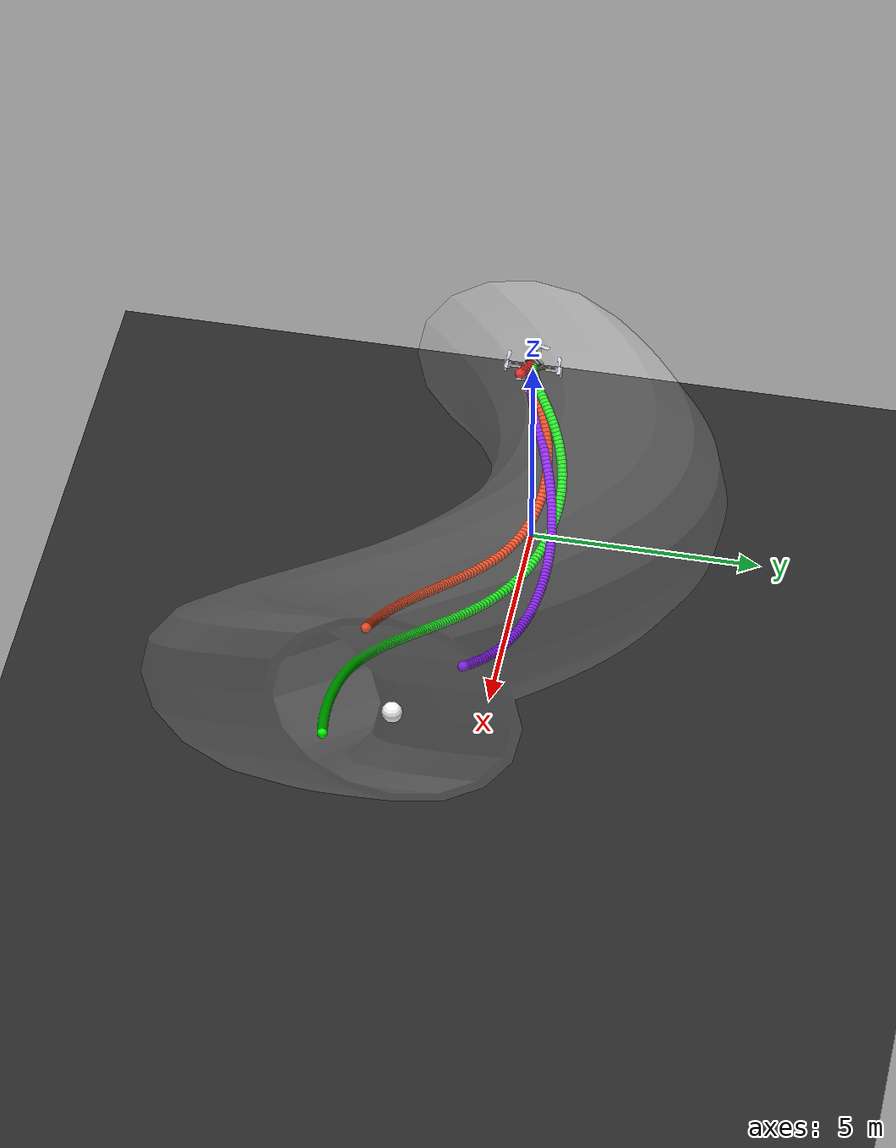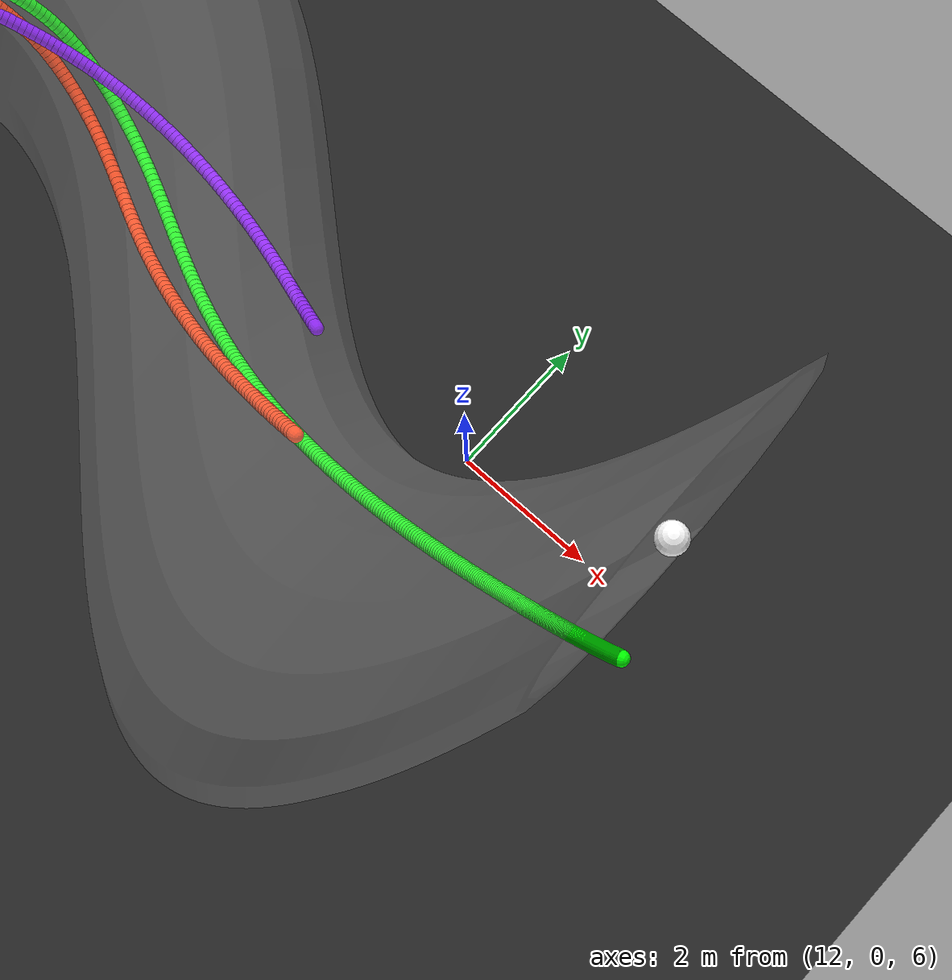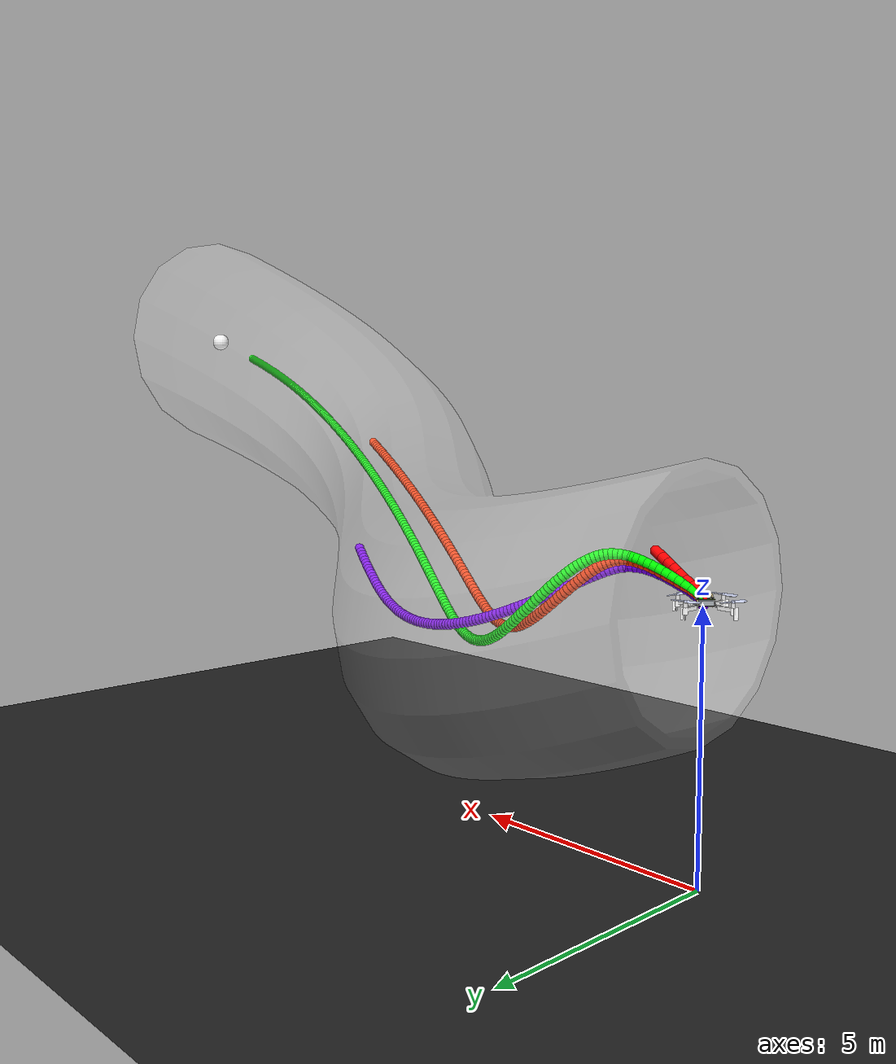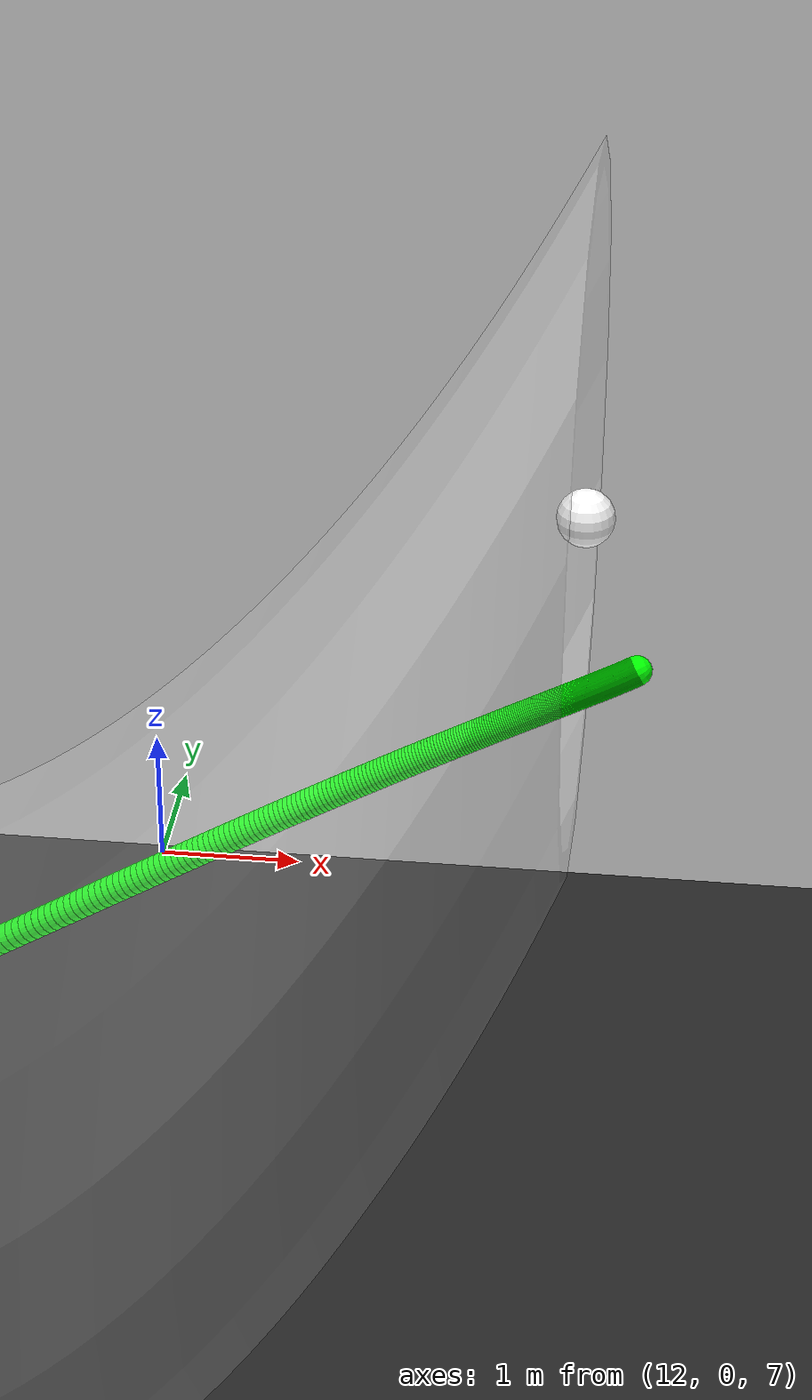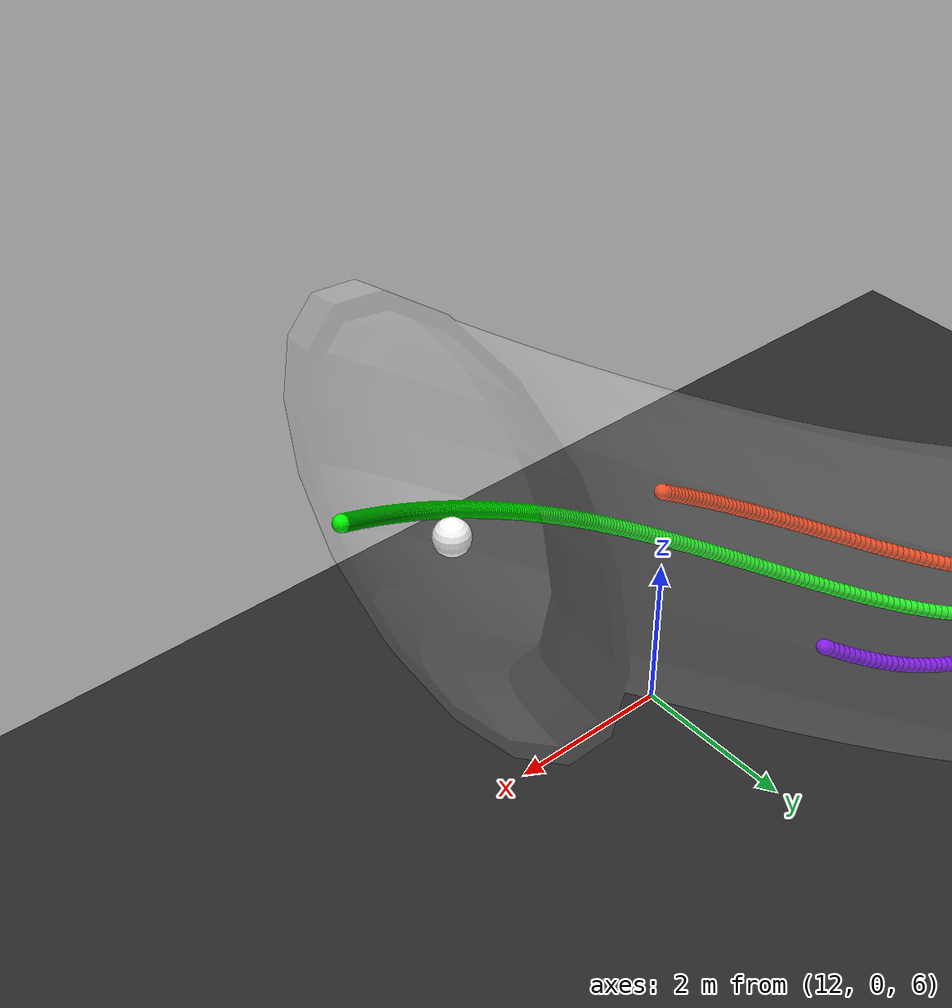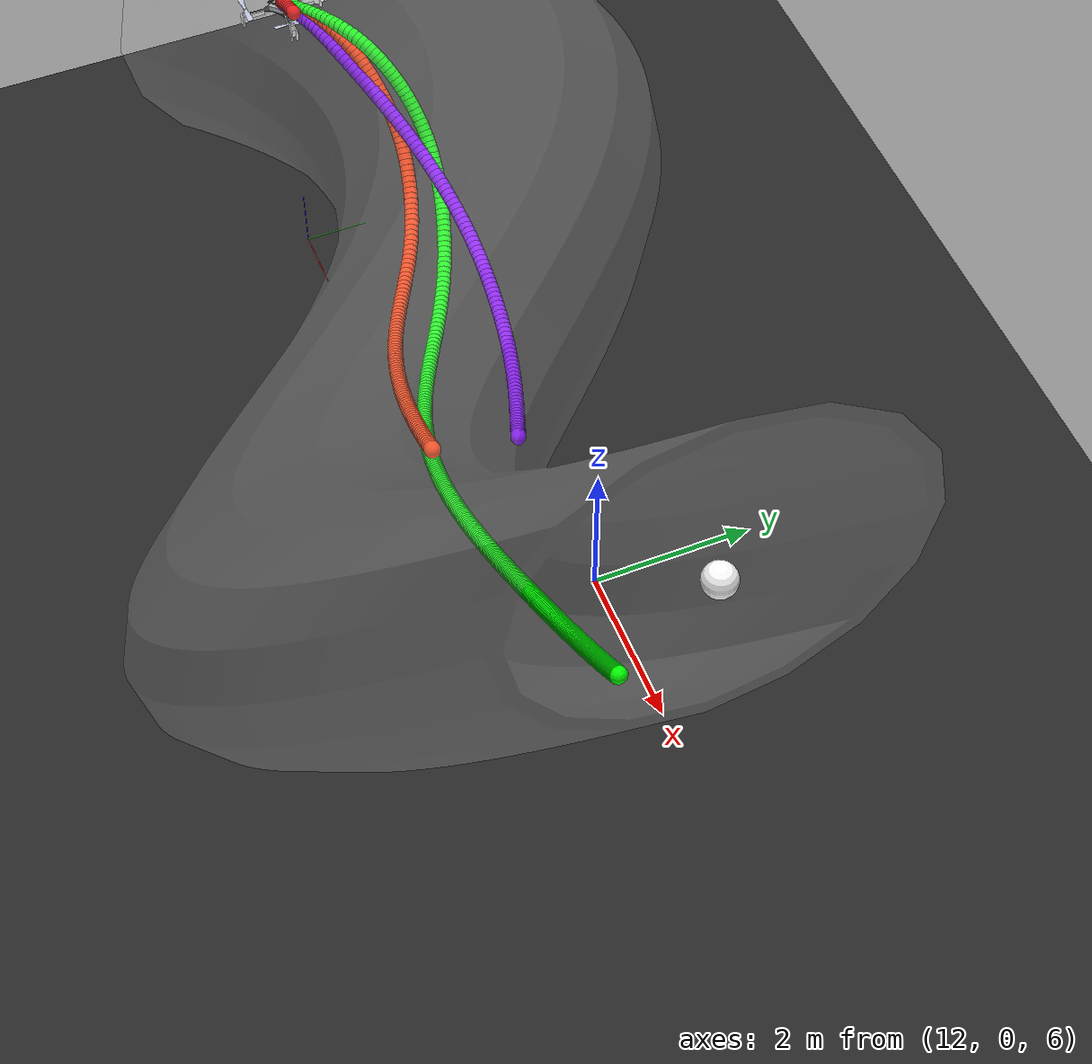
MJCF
<mujoco model="CF2 scene">
  <include file="cf2.xml" />

  <statistic center="0 0 0.1" extent="0.2" meansize=".05" />

  <visual>

    <rgba haze="0.15 0.25 0.35 0" />
    <global azimuth="-20" elevation="-20" ellipsoidinertia="true" />
    <map zfar="1000" />
  </visual>

  <asset>
    <mesh name="tunnel" file="tube_thick.obj" scale="1.0 1.0 1.0" />
    <texture type="skybox" builtin="gradient" rgb1="0.3 0.5 0.7" rgb2="0 0 0" width="512" height="3072" />

    <texture type="2d" name="groundplane" builtin="checker" mark="edge" rgb1="0.1 0.1 0.1" rgb2="0.2 0.2 0.2" markrgb="0.8 0.8 0.8" width="300" height="300" />

    <material name="groundplane" texture="groundplane" texuniform="true" texrepeat="5 5" reflectance="0.1" />
  </asset>

  <worldbody>
    <light diffuse="1 1 1" ambient="1 1 1" pos="0 0 100" dir="0 0 -1" directional="false" castshadow="false" />

    <geom name="floor" size="0 0 0.05" type="plane" material="groundplane" />
    <site name="x_axis" size="0.005" type="cylinder" fromto="0 0 0 1 0 0" rgba="1 0 0 1" />
    <site name="y_axis" size="0.005" type="cylinder" fromto="0 0 0 0 1 0" rgba="0 1 0 1" />
    <site name="z_axis" size="0.005" type="cylinder" fromto="0 0 0 0 0 1" rgba="0 0 1 1" />

    <site name="target" size="0.2" type="sphere" pos="15 0 10" rgba="1 1 1 1" />

    <camera name="cam_aux" pos="-3.429 -18.876 13.649" xyaxes="0.874 -0.486 -0.000 0.179 0.321 0.930" />
    <camera name="cam_traj_1" pos="-7.863 -0.826 23.122" xyaxes="0.020 -1.000 0.000 0.737 0.014 0.676" />
    <camera name="cam_traj_2" pos="7.041 -14.560 20.718" xyaxes="1.000 -0.031 -0.000 0.021 0.691 0.722" />
    <camera name="cam_traj_3" pos="-11.538 -0.602 8.690" xyaxes="0.046 -0.999 -0.000 0.161 0.007 0.987"/>

    <body name="tunnel" pos="0.0 0.0 0.0" quat="1 0 0 0">
         <geom name="tunnel" type="mesh" mesh="tunnel" pos="-0.0 0.0 0.029" quat="1 0 0 0" rgba="1 1 1 0.05" />
    </body>

  <body name="trajectory_0" pos="0 0 0"><geom type="capsule" fromto="0.005024605410812866 -0.0004147894235280043 5.051189149415158 0.03790216746712222 -0.0033566713637193137 5.135572800704954" size="0.1" rgba="1 0 0 1" /><geom type="capsule" fromto="0.03790216746712222 -0.0033566713637193137 5.135572800704954 0.13010258885838488 -0.01009048150116365 5.236266690172134" size="0.1" rgba="1 0 0 1" /><geom type="capsule" fromto="0.13010258885838488 -0.01009048150116365 5.236266690172134 0.26294506276311325 -0.019231826013760653 5.332305607285237" size="0.1" rgba="1 0 0 1" /><geom type="capsule" fromto="0.26294506276311325 -0.019231826013760653 5.332305607285237 0.4091732524023872 -0.03080936178915821 5.4182422421014875" size="0.1" rgba="1 0 0 1" /><geom type="capsule" fromto="0.4091732524023872 -0.03080936178915821 5.4182422421014875 0.5501763580848618 -0.044253772169157296 5.507680150321134" size="0.1" rgba="1 0 0 1" /><geom type="capsule" fromto="0.5501763580848618 -0.044253772169157296 5.507680150321134 0.6820177646593318 -0.058268083256777854 5.5927199867393576" size="0.1" rgba="1 0 0 1" /><geom type="capsule" fromto="0.6820177646593318 -0.058268083256777854 5.5927199867393576 0.8127607506839103 -0.07226709273045118 5.674749799785284" size="0.1" rgba="1 0 0 1" /><geom type="capsule" fromto="0.8127607506839103 -0.07226709273045118 5.674749799785284 0.9454678738498982 -0.08602278785444555 5.75699548738207" size="0.1" rgba="1 0 0 1" /><geom type="capsule" fromto="0.9454678738498982 -0.08602278785444555 5.75699548738207 1.0775540655088136 -0.09944100626499146 5.838976914517452" size="0.1" rgba="1 0 0 1" /></body><body name="trajectory_1" pos="0 0 0"><geom type="capsule" fromto="0.004079218832733524 0.000369304007222971 5.036228656554201 0.034410999647552135 0.003386690718077548 5.097169335923788" size="0.1" rgba="0.5 0.0 1.0 1" /><geom type="capsule" fromto="0.034410999647552135 0.003386690718077548 5.097169335923788 0.11802009602138715 0.010830227152276753 5.169094152804735" size="0.1" rgba="0.5 0.0 1.0 1" /><geom type="capsule" fromto="0.11802009602138715 0.010830227152276753 5.169094152804735 0.23740686414685702 0.021277380510837947 5.237064967284532" size="0.1" rgba="0.5 0.0 1.0 1" /><geom type="capsule" fromto="0.23740686414685702 0.021277380510837947 5.237064967284532 0.36538567007016265 0.03407265556915245 5.290961090655026" size="0.1" rgba="0.5 0.0 1.0 1" /><geom type="capsule" fromto="0.36538567007016265 0.03407265556915245 5.290961090655026 0.4888879292658142 0.04907234262312233 5.343594957711468" size="0.1" rgba="0.5 0.0 1.0 1" /><geom type="capsule" fromto="0.4888879292658142 0.04907234262312233 5.343594957711468 0.6043202319572154 0.06545808628177216 5.392396074441798" size="0.1" rgba="0.5 0.0 1.0 1" /><geom type="capsule" fromto="0.6043202319572154 0.06545808628177216 5.392396074441798 0.7152518907430054 0.08262764745122234 5.4360402317384" size="0.1" rgba="0.5 0.0 1.0 1" /><geom type="capsule" fromto="0.7152518907430054 0.08262764745122234 5.4360402317384 0.824009401678503 0.10033008482917541 5.474268553816616" size="0.1" rgba="0.5 0.0 1.0 1" /><geom type="capsule" fromto="0.824009401678503 0.10033008482917541 5.474268553816616 0.9301786713326132 0.11858869144756455 5.506453778919983" size="0.1" rgba="0.5 0.0 1.0 1" /><geom type="capsule" fromto="0.9301786713326132 0.11858869144756455 5.506453778919983 1.032780900642003 0.13757953442834572 5.531991085522639" size="0.1" rgba="0.5 0.0 1.0 1" /><geom type="capsule" fromto="1.032780900642003 0.13757953442834572 5.531991085522639 1.1314586760277234 0.1575254572644415 5.550484746549378" size="0.1" rgba="0.5 0.0 1.0 1" /><geom type="capsule" fromto="1.1314586760277234 0.1575254572644415 5.550484746549378 1.2262916174255953 0.17865017536371267 5.561618463748745" size="0.1" rgba="0.5 0.0 1.0 1" /><geom type="capsule" fromto="1.2262916174255953 0.17865017536371267 5.561618463748745 1.317477837784216 0.20116658817488633 5.565250034117393" size="0.1" rgba="0.5 0.0 1.0 1" /><geom type="capsule" fromto="1.317477837784216 0.20116658817488633 5.565250034117393 1.405251843358714 0.2252571959445097 5.56148961626999" size="0.1" rgba="0.5 0.0 1.0 1" /><geom type="capsule" fromto="1.405251843358714 0.2252571959445097 5.56148961626999 1.4899192076581091 0.2510420024809921 5.550716910339737" size="0.1" rgba="0.5 0.0 1.0 1" /><geom type="capsule" fromto="1.4899192076581091 0.2510420024809921 5.550716910339737 1.5718663831642927 0.27854912551628686 5.533533621944337" size="0.1" rgba="0.5 0.0 1.0 1" /><geom type="capsule" fromto="1.5718663831642927 0.27854912551628686 5.533533621944337 1.651529429939126 0.3077029145790112 5.510692260121318" size="0.1" rgba="0.5 0.0 1.0 1" /><geom type="capsule" fromto="1.651529429939126 0.3077029145790112 5.510692260121318 1.7293742059233241 0.33833862878429116 5.483112024311284" size="0.1" rgba="0.5 0.0 1.0 1" /><geom type="capsule" fromto="1.7293742059233241 0.33833862878429116 5.483112024311284 1.8058667235639545 0.37022949936442606 5.451831758381821" size="0.1" rgba="0.5 0.0 1.0 1" /><geom type="capsule" fromto="1.8058667235639545 0.37022949936442606 5.451831758381821 1.8813961839736828 0.4031077736851897 5.417744203113499" size="0.1" rgba="0.5 0.0 1.0 1" /><geom type="capsule" fromto="1.8813961839736828 0.4031077736851897 5.417744203113499 1.95626143862728 0.43669473448065754 5.381545602661202" size="0.1" rgba="0.5 0.0 1.0 1" /><geom type="capsule" fromto="1.95626143862728 0.43669473448065754 5.381545602661202 2.0306926308136166 0.4707258474135949 5.3437966201584155" size="0.1" rgba="0.5 0.0 1.0 1" /><geom type="capsule" fromto="2.0306926308136166 0.4707258474135949 5.3437966201584155 2.104866585814905 0.5049621353640296 5.304950600639018" size="0.1" rgba="0.5 0.0 1.0 1" /><geom type="capsule" fromto="2.104866585814905 0.5049621353640296 5.304950600639018 2.178918310895949 0.5391935907562525 5.265372971141344" size="0.1" rgba="0.5 0.0 1.0 1" /><geom type="capsule" fromto="2.178918310895949 0.5391935907562525 5.265372971141344 2.2529497167967456 0.57323863186612 5.225357198128634" size="0.1" rgba="0.5 0.0 1.0 1" /><geom type="capsule" fromto="2.2529497167967456 0.57323863186612 5.225357198128634 2.3270365264286834 0.6069418158271803 5.185138149532053" size="0.1" rgba="0.5 0.0 1.0 1" /><geom type="capsule" fromto="2.3270365264286834 0.6069418158271803 5.185138149532053 2.4012339125855693 0.6401709600772735 5.144903159048769" size="0.1" rgba="0.5 0.0 1.0 1" /><geom type="capsule" fromto="2.4012339125855693 0.6401709600772735 5.144903159048769 2.4755810957812105 0.672814228839852 5.104801126799339" size="0.1" rgba="0.5 0.0 1.0 1" /><geom type="capsule" fromto="2.4755810957812105 0.672814228839852 5.104801126799339 2.550105038891869 0.7047774182998339 5.064949976794993" size="0.1" rgba="0.5 0.0 1.0 1" /><geom type="capsule" fromto="2.550105038891869 0.7047774182998339 5.064949976794993 2.6248233798672858 0.735981516759516 5.025442756878525" size="0.1" rgba="0.5 0.0 1.0 1" /><geom type="capsule" fromto="2.6248233798672858 0.735981516759516 5.025442756878525 2.699746747718469 0.7663605496537952 4.98635262812376" size="0.1" rgba="0.5 0.0 1.0 1" /><geom type="capsule" fromto="2.699746747718469 0.7663605496537952 4.98635262812376 2.7748805895357167 0.7958596950430997 4.9477369497800545" size="0.1" rgba="0.5 0.0 1.0 1" /><geom type="capsule" fromto="2.7748805895357167 0.7958596950430997 4.9477369497800545 2.850226610361106 0.8244336471238778 4.9096406262978585" size="0.1" rgba="0.5 0.0 1.0 1" /><geom type="capsule" fromto="2.850226610361106 0.8244336471238778 4.9096406262978585 2.92578390480553 0.8520452026964611 4.872098849146541" size="0.1" rgba="0.5 0.0 1.0 1" /><geom type="capsule" fromto="2.92578390480553 0.8520452026964611 4.872098849146541 3.0015498422445686 0.8786640450541928 4.835139339624094" size="0.1" rgba="0.5 0.0 1.0 1" /><geom type="capsule" fromto="3.0015498422445686 0.8786640450541928 4.835139339624094 3.0775207549131522 0.9042657005131598 4.7987841787538645" size="0.1" rgba="0.5 0.0 1.0 1" /><geom type="capsule" fromto="3.0775207549131522 0.9042657005131598 4.7987841787538645 3.1536924685719585 0.9288306443827385 4.7630512949961705" size="0.1" rgba="0.5 0.0 1.0 1" /><geom type="capsule" fromto="3.1536924685719585 0.9288306443827385 4.7630512949961705 3.230060707826563 0.9523435352215069 4.727955668416212" size="0.1" rgba="0.5 0.0 1.0 1" /><geom type="capsule" fromto="3.230060707826563 0.9523435352215069 4.727955668416212 3.306621401849789 0.9747925584230869 4.693510300508022" size="0.1" rgba="0.5 0.0 1.0 1" /><geom type="capsule" fromto="3.306621401849789 0.9747925584230869 4.693510300508022 3.383370910779365 0.996168862331934 4.659726990990161" size="0.1" rgba="0.5 0.0 1.0 1" /><geom type="capsule" fromto="3.383370910779365 0.996168862331934 4.659726990990161 3.4603061894803995 1.0164660721261256 4.626616955793007" size="0.1" rgba="0.5 0.0 1.0 1" /><geom type="capsule" fromto="3.4603061894803995 1.0164660721261256 4.626616955793007 3.537424902820306 1.0356798685895345 4.5941913156258956" size="0.1" rgba="0.5 0.0 1.0 1" /><geom type="capsule" fromto="3.537424902820306 1.0356798685895345 4.5941913156258956 3.6147255035665533 1.0538076205681803 4.5624614801346075" size="0.1" rgba="0.5 0.0 1.0 1" /><geom type="capsule" fromto="3.6147255035665533 1.0538076205681803 4.5624614801346075 3.692207281512973 1.0708480613848121 4.531439448182631" size="0.1" rgba="0.5 0.0 1.0 1" /><geom type="capsule" fromto="3.692207281512973 1.0708480613848121 4.531439448182631 3.7698703908231006 1.0868010007954108 4.501138041661371" size="0.1" rgba="0.5 0.0 1.0 1" /><geom type="capsule" fromto="3.7698703908231006 1.0868010007954108 4.501138041661371 3.8477158612952262 1.1016670652095866 4.471571087534925" size="0.1" rgba="0.5 0.0 1.0 1" /><geom type="capsule" fromto="3.8477158612952262 1.1016670652095866 4.471571087534925 3.925745598156549 1.1154474598786106 4.442753560490771" size="0.1" rgba="0.5 0.0 1.0 1" /><geom type="capsule" fromto="3.925745598156549 1.1154474598786106 4.442753560490771 4.003962374068924 1.128143747591155 4.4147016965886365" size="0.1" rgba="0.5 0.0 1.0 1" /><geom type="capsule" fromto="4.003962374068924 1.128143747591155 4.4147016965886365 4.082369816276019 1.1397576391151194 4.387433086656591" size="0.1" rgba="0.5 0.0 1.0 1" /><geom type="capsule" fromto="4.082369816276019 1.1397576391151194 4.387433086656591 4.160972391222801 1.1502907911913096 4.360966756839699" size="0.1" rgba="0.5 0.0 1.0 1" /><geom type="capsule" fromto="4.160972391222801 1.1502907911913096 4.360966756839699 4.239775388506295 1.159744608327835 4.335323242623523" size="0.1" rgba="0.5 0.0 1.0 1" /><geom type="capsule" fromto="4.239775388506295 1.159744608327835 4.335323242623523 4.318784905647876 1.1681200449677094 4.310524661800657" size="0.1" rgba="0.5 0.0 1.0 1" /><geom type="capsule" fromto="4.318784905647876 1.1681200449677094 4.310524661800657 4.398007834894378 1.1754174048083321 4.286594791200045" size="0.1" rgba="0.5 0.0 1.0 1" /><geom type="capsule" fromto="4.398007834894378 1.1754174048083321 4.286594791200045 4.477451853045476 1.1816361341388881 4.263559151539784" size="0.1" rgba="0.5 0.0 1.0 1" /><geom type="capsule" fromto="4.477451853045476 1.1816361341388881 4.263559151539784 4.557125415158422 1.1867746060248618 4.241445104483677" size="0.1" rgba="0.5 0.0 1.0 1" /><geom type="capsule" fromto="4.557125415158422 1.1867746060248618 4.241445104483677 4.637037752890429 1.1908298919975848 4.220281965871705" size="0.1" rgba="0.5 0.0 1.0 1" /><geom type="capsule" fromto="4.637037752890429 1.1908298919975848 4.220281965871705 4.71719813679634 1.1937975368370084 4.200098341662973" size="0.1" rgba="0.5 0.0 1.0 1" /><geom type="capsule" fromto="4.71719813679634 1.1937975368370084 4.200098341662973 4.797614741377785 1.1956713256667937 4.180917968621146" size="0.1" rgba="0.5 0.0 1.0 1" /><geom type="capsule" fromto="4.797614741377785 1.1956713256667937 4.180917968621146 4.878295814722575 1.1964438796135384 4.162764386164204" size="0.1" rgba="0.5 0.0 1.0 1" /><geom type="capsule" fromto="4.878295814722575 1.1964438796135384 4.162764386164204 4.9592503835790565 1.1961145523569385 4.145664462178894" size="0.1" rgba="0.5 0.0 1.0 1" /><geom type="capsule" fromto="4.9592503835790565 1.1961145523569385 4.145664462178894 5.040487909187953 1.1946956281593328 4.129647922020847" size="0.1" rgba="0.5 0.0 1.0 1" /><geom type="capsule" fromto="5.040487909187953 1.1946956281593328 4.129647922020847 5.122018087447468 1.1922095342014976 4.114747058781677" size="0.1" rgba="0.5 0.0 1.0 1" /><geom type="capsule" fromto="5.122018087447468 1.1922095342014976 4.114747058781677 5.203850580217675 1.1886835336315391 4.100996151010571" size="0.1" rgba="0.5 0.0 1.0 1" /><geom type="capsule" fromto="5.203850580217675 1.1886835336315391 4.100996151010571 5.285994790335234 1.184144907887848 4.088430887247395" size="0.1" rgba="0.5 0.0 1.0 1" /><geom type="capsule" fromto="5.285994790335234 1.184144907887848 4.088430887247395 5.368459805244199 1.1786178540890753 4.077088402985317" size="0.1" rgba="0.5 0.0 1.0 1" /><geom type="capsule" fromto="5.368459805244199 1.1786178540890753 4.077088402985317 5.451254357528738 1.1721219990475393 4.067007500217504" size="0.1" rgba="0.5 0.0 1.0 1" /><geom type="capsule" fromto="5.451254357528738 1.1721219990475393 4.067007500217504 5.534386733162483 1.1646720115378866 4.058228804701545" size="0.1" rgba="0.5 0.0 1.0 1" /><geom type="capsule" fromto="5.534386733162483 1.1646720115378866 4.058228804701545 5.617864630197958 1.156277836118252 4.050794837801903" size="0.1" rgba="0.5 0.0 1.0 1" /><geom type="capsule" fromto="5.617864630197958 1.156277836118252 4.050794837801903 5.701694979614621 1.1469452246540526 4.04475002381794" size="0.1" rgba="0.5 0.0 1.0 1" /><geom type="capsule" fromto="5.701694979614621 1.1469452246540526 4.04475002381794 5.7858837339877205 1.1366763777931765 4.040140647744672" size="0.1" rgba="0.5 0.0 1.0 1" /><geom type="capsule" fromto="5.7858837339877205 1.1366763777931765 4.040140647744672 5.8704356252066265 1.125470602604728 4.037014768054228" size="0.1" rgba="0.5 0.0 1.0 1" /><geom type="capsule" fromto="5.8704356252066265 1.125470602604728 4.037014768054228 5.955353890816717 1.1133249498943973 4.035422081738411" size="0.1" rgba="0.5 0.0 1.0 1" /><geom type="capsule" fromto="5.955353890816717 1.1133249498943973 4.035422081738411 6.040639968146904 1.1002348262268609 4.0354137336005955" size="0.1" rgba="0.5 0.0 1.0 1" /><geom type="capsule" fromto="6.040639968146904 1.1002348262268609 4.0354137336005955 6.126293155620137 1.0861945908580195 4.037042057965407" size="0.1" rgba="0.5 0.0 1.0 1" /><geom type="capsule" fromto="6.126293155620137 1.0861945908580195 4.037042057965407 6.212310241599069 1.071198153376495 4.0403602385033155" size="0.1" rgba="0.5 0.0 1.0 1" /><geom type="capsule" fromto="6.212310241599069 1.071198153376495 4.0403602385033155 6.298685102937122 1.0552395882073795 4.045421870703627" size="0.1" rgba="0.5 0.0 1.0 1" /><geom type="capsule" fromto="6.298685102937122 1.0552395882073795 4.045421870703627 6.385408278136811 1.038313779709506 4.052280411645695" size="0.1" rgba="0.5 0.0 1.0 1" /><geom type="capsule" fromto="6.385408278136811 1.038313779709506 4.052280411645695 6.47246652365728 1.0204171075916153 4.060988503241976" size="0.1" rgba="0.5 0.0 1.0 1" /><geom type="capsule" fromto="6.47246652365728 1.0204171075916153 4.060988503241976 6.5598423664203995 1.001548177194131 4.0715971583855985" size="0.1" rgba="0.5 0.0 1.0 1" /><geom type="capsule" fromto="6.5598423664203995 1.001548177194131 4.0715971583855985 6.647513670816385 0.9817085928437592 4.084154804886403" size="0.1" rgba="0.5 0.0 1.0 1" /><geom type="capsule" fromto="6.647513670816385 0.9817085928437592 4.084154804886403 6.735453244220431 0.9609037648829242 4.098706190173773" size="0.1" rgba="0.5 0.0 1.0 1" /><geom type="capsule" fromto="6.735453244220431 0.9609037648829242 4.098706190173773 6.823628510674528 0.939143732100769 4.115291160754518" size="0.1" rgba="0.5 0.0 1.0 1" /><geom type="capsule" fromto="6.823628510674528 0.939143732100769 4.115291160754518 6.912001287142511 0.9164439714220647 4.13394334423111" size="0.1" rgba="0.5 0.0 1.0 1" /><geom type="capsule" fromto="6.912001287142511 0.9164439714220647 4.13394334423111 7.000527699501544 0.8928261565435677 4.1546887776042" size="0.1" rgba="0.5 0.0 1.0 1" /><geom type="capsule" fromto="7.000527699501544 0.8928261565435677 4.1546887776042 7.089158274888497 0.8683188179536733 4.177544542123777" size="0.1" rgba="0.5 0.0 1.0 1" /><geom type="capsule" fromto="7.089158274888497 0.8683188179536733 4.177544542123777 7.17783824190652 0.842957850131801 4.202517479809559" size="0.1" rgba="0.5 0.0 1.0 1" /><geom type="capsule" fromto="7.17783824190652 0.842957850131801 4.202517479809559 7.2665080596311995 0.8167868097068808 4.2296030769808795" size="0.1" rgba="0.5 0.0 1.0 1" /><geom type="capsule" fromto="7.2665080596311995 0.8167868097068808 4.2296030769808795 7.3551041802638375 0.7898569528865639 4.258784602605687" size="0.1" rgba="0.5 0.0 1.0 1" /><geom type="capsule" fromto="7.3551041802638375 0.7898569528865639 4.258784602605687 7.443560029774646 0.7622269728309337 4.29003258149617" size="0.1" rgba="0.5 0.0 1.0 1" /><geom type="capsule" fromto="7.443560029774646 0.7622269728309337 4.29003258149617 7.5318071684036605 0.7339624178534515 4.323304663352936" size="0.1" rgba="0.5 0.0 1.0 1" /><geom type="capsule" fromto="7.5318071684036605 0.7339624178534515 4.323304663352936 7.619776571958279 0.7051347976928486 4.358545919617616" size="0.1" rgba="0.5 0.0 1.0 1" /><geom type="capsule" fromto="7.619776571958279 0.7051347976928486 4.358545919617616 7.707399959346897 0.6758204141776427 4.395689564652439" size="0.1" rgba="0.5 0.0 1.0 1" /><geom type="capsule" fromto="7.707399959346897 0.6758204141776427 4.395689564652439 7.794611084954808 0.6460989797590022 4.434658061333" size="0.1" rgba="0.5 0.0 1.0 1" /><geom type="capsule" fromto="7.794611084954808 0.6460989797590022 4.434658061333 7.881346917855419 0.6160521067525426 4.475364539424763" size="0.1" rgba="0.5 0.0 1.0 1" /><geom type="capsule" fromto="7.881346917855419 0.6160521067525426 4.475364539424763 7.967548643268266 0.5857617602056537 4.517714435053724" size="0.1" rgba="0.5 0.0 1.0 1" /><geom type="capsule" fromto="7.967548643268266 0.5857617602056537 4.517714435053724 8.053162441803345 0.5553087721516343 4.5616072499283495" size="0.1" rgba="0.5 0.0 1.0 1" /><geom type="capsule" fromto="8.053162441803345 0.5553087721516343 4.5616072499283495 8.138140024515733 0.5247714998061813 4.606938325366064" size="0.1" rgba="0.5 0.0 1.0 1" /><geom type="capsule" fromto="8.138140024515733 0.5247714998061813 4.606938325366064 8.222438926007165 0.49422468252071644 4.6536005475392255" size="0.1" rgba="0.5 0.0 1.0 1" /><geom type="capsule" fromto="8.222438926007165 0.49422468252071644 4.6536005475392255 8.306022576299439 0.46373853080001814 4.701485922235045" size="0.1" rgba="0.5 0.0 1.0 1" /><geom type="capsule" fromto="8.306022576299439 0.46373853080001814 4.701485922235045 8.388860183777348 0.4333780605277986 4.7504869717935065" size="0.1" rgba="0.5 0.0 1.0 1" /><geom type="capsule" fromto="8.388860183777348 0.4333780605277986 4.7504869717935065 8.470926468729019 0.40320266608431843 4.800497928244192" size="0.1" rgba="0.5 0.0 1.0 1" /><geom type="capsule" fromto="8.470926468729019 0.40320266608431843 4.800497928244192 8.552201288510135 0.3732659107368471 4.851415714883856" size="0.1" rgba="0.5 0.0 1.0 1" /><geom type="capsule" fromto="8.552201288510135 0.3732659107368471 4.851415714883856 8.63266919262071 0.3436155030193341 4.903140721919245" size="0.1" rgba="0.5 0.0 1.0 1" /><geom type="capsule" fromto="8.63266919262071 0.3436155030193341 4.903140721919245 8.712318940811755 0.3142934234646755 4.955577390966985" size="0.1" rgba="0.5 0.0 1.0 1" /><geom type="capsule" fromto="8.712318940811755 0.3142934234646755 4.955577390966985 8.79114301106195 0.28533616584985705 5.008634628753808" size="0.1" rgba="0.5 0.0 1.0 1" /><geom type="capsule" fromto="8.79114301106195 0.28533616584985705 5.008634628753808 8.869137117833407 0.256775059721877 5.062226073020836" size="0.1" rgba="0.5 0.0 1.0 1" /><geom type="capsule" fromto="8.869137117833407 0.256775059721877 5.062226073020836 8.94629975506734 0.22863664520608357 5.116270234150678" size="0.1" rgba="0.5 0.0 1.0 1" /><geom type="capsule" fromto="8.94629975506734 0.22863664520608357 5.116270234150678 9.022631773275641 0.20094307603899653 5.1706905350821035" size="0.1" rgba="0.5 0.0 1.0 1" /></body><body name="trajectory_2" pos="0 0 0"><geom type="capsule" fromto="0.00437318461997022 0.0007496481513081153 5.041824115472996 0.035507787889569806 0.0065076702425278425 5.1121089997573925" size="0.1" rgba="1 0.2 0.0 1" /><geom type="capsule" fromto="0.035507787889569806 0.0065076702425278425 5.1121089997573925 0.1210112411277036 0.020053517274669783 5.194186137735673" size="0.1" rgba="1 0.2 0.0 1" /><geom type="capsule" fromto="0.1210112411277036 0.020053517274669783 5.194186137735673 0.24191192169104436 0.038361705149055514 5.269635358225623" size="0.1" rgba="1 0.2 0.0 1" /><geom type="capsule" fromto="0.24191192169104436 0.038361705149055514 5.269635358225623 0.371237064352328 0.06046459106241012 5.329949473255537" size="0.1" rgba="1 0.2 0.0 1" /><geom type="capsule" fromto="0.371237064352328 0.06046459106241012 5.329949473255537 0.4960559123805818 0.08575803235701035 5.39042847048231" size="0.1" rgba="1 0.2 0.0 1" /><geom type="capsule" fromto="0.4960559123805818 0.08575803235701035 5.39042847048231 0.6126201672110702 0.11238564114516242 5.447935754945297" size="0.1" rgba="1 0.2 0.0 1" /><geom type="capsule" fromto="0.6126201672110702 0.11238564114516242 5.447935754945297 0.7246534858527274 0.13933713829521055 5.500546023519756" size="0.1" rgba="1 0.2 0.0 1" /><geom type="capsule" fromto="0.7246534858527274 0.13933713829521055 5.500546023519756 0.8343733132124811 0.1663537347999242 5.547736569716039" size="0.1" rgba="1 0.2 0.0 1" /><geom type="capsule" fromto="0.8343733132124811 0.1663537347999242 5.547736569716039 0.9410720344646984 0.1935353068848628 5.588925691976844" size="0.1" rgba="1 0.2 0.0 1" /><geom type="capsule" fromto="0.9410720344646984 0.1935353068848628 5.588925691976844 1.0436027114296775 0.221088251164813 5.623661915483553" size="0.1" rgba="1 0.2 0.0 1" /><geom type="capsule" fromto="1.0436027114296775 0.221088251164813 5.623661915483553 1.1415208374446724 0.24918003639943764 5.65143417859452" size="0.1" rgba="1 0.2 0.0 1" /><geom type="capsule" fromto="1.1415208374446724 0.24918003639943764 5.65143417859452 1.234771626297441 0.27791061495549507 5.671529936545685" size="0.1" rgba="1 0.2 0.0 1" /><geom type="capsule" fromto="1.234771626297441 0.27791061495549507 5.671529936545685 1.323379305785619 0.307327491582333 5.6833294686906015" size="0.1" rgba="1 0.2 0.0 1" /><geom type="capsule" fromto="1.323379305785619 0.307327491582333 5.6833294686906015 1.4074288443399736 0.3374201497584872 5.686475153358069" size="0.1" rgba="1 0.2 0.0 1" /><geom type="capsule" fromto="1.4074288443399736 0.3374201497584872 5.686475153358069 1.487131799655383 0.36810395500107257 5.680870640505144" size="0.1" rgba="1 0.2 0.0 1" /><geom type="capsule" fromto="1.487131799655383 0.36810395500107257 5.680870640505144 1.5628358730730079 0.3992172474456516 5.666622760258016" size="0.1" rgba="1 0.2 0.0 1" /><geom type="capsule" fromto="1.5628358730730079 0.3992172474456516 5.666622760258016 1.6350119538934433 0.4305420072749385 5.6441209133965815" size="0.1" rgba="1 0.2 0.0 1" /><geom type="capsule" fromto="1.6350119538934433 0.4305420072749385 5.6441209133965815 1.7042877161156027 0.46184551819596065 5.614424281223033" size="0.1" rgba="1 0.2 0.0 1" /><geom type="capsule" fromto="1.7042877161156027 0.46184551819596065 5.614424281223033 1.771317339765524 0.49288495069435473 5.578819753420225" size="0.1" rgba="1 0.2 0.0 1" /><geom type="capsule" fromto="1.771317339765524 0.49288495069435473 5.578819753420225 1.8366512493963505 0.5234109300044573 5.5383226369037" size="0.1" rgba="1 0.2 0.0 1" /><geom type="capsule" fromto="1.8366512493963505 0.5234109300044573 5.5383226369037 1.9007446660616139 0.5531888551284555 5.4937818176106665" size="0.1" rgba="1 0.2 0.0 1" /><geom type="capsule" fromto="1.9007446660616139 0.5531888551284555 5.4937818176106665 1.963975452457065 0.5820050468092467 5.445931700336022" size="0.1" rgba="1 0.2 0.0 1" /><geom type="capsule" fromto="1.963975452457065 0.5820050468092467 5.445931700336022 2.0266566119722698 0.6096663593815314 5.3954029030314965" size="0.1" rgba="1 0.2 0.0 1" /><geom type="capsule" fromto="2.0266566119722698 0.6096663593815314 5.3954029030314965 2.089047277373054 0.6359987975395142 5.342740141638795" size="0.1" rgba="1 0.2 0.0 1" /><geom type="capsule" fromto="2.089047277373054 0.6359987975395142 5.342740141638795 2.1513615539172495 0.6608456558822791 5.2884174843528555" size="0.1" rgba="1 0.2 0.0 1" /><geom type="capsule" fromto="2.1513615539172495 0.6608456558822791 5.2884174843528555 2.213775937508471 0.6840655063137996 5.232849785075494" size="0.1" rgba="1 0.2 0.0 1" /><geom type="capsule" fromto="2.213775937508471 0.6840655063137996 5.232849785075494 2.2764358460537903 0.7055301867489743 5.176401769223376" size="0.1" rgba="1 0.2 0.0 1" /><geom type="capsule" fromto="2.2764358460537903 0.7055301867489743 5.176401769223376 2.3394613922499325 0.7251228028106721 5.119395539131308" size="0.1" rgba="1 0.2 0.0 1" /><geom type="capsule" fromto="2.3394613922499325 0.7251228028106721 5.119395539131308 2.402952430536104 0.7427357135498209 5.062117026149087" size="0.1" rgba="1 0.2 0.0 1" /><geom type="capsule" fromto="2.402952430536104 0.7427357135498209 5.062117026149087 2.4669929102512618 0.7582684624756416 5.004821694491295" size="0.1" rgba="1 0.2 0.0 1" /><geom type="capsule" fromto="2.4669929102512618 0.7582684624756416 5.004821694491295 2.5316545931243093 0.7716256122341543 4.947739679440857" size="0.1" rgba="1 0.2 0.0 1" /><geom type="capsule" fromto="2.5316545931243093 0.7716256122341543 4.947739679440857 2.5970002151103486 0.7827144351776266 4.891080486664054" size="0.1" rgba="1 0.2 0.0 1" /><geom type="capsule" fromto="2.5970002151103486 0.7827144351776266 4.891080486664054 2.6630861845446376 0.7914423996175979 4.83503735787985" size="0.1" rgba="1 0.2 0.0 1" /><geom type="capsule" fromto="2.6630861845446376 0.7914423996175979 4.83503735787985 2.7299649133509503 0.797714370982354 4.779791405493137" size="0.1" rgba="1 0.2 0.0 1" /><geom type="capsule" fromto="2.7299649133509503 0.797714370982354 4.779791405493137 2.7976868793336878 0.8014294157437495 4.725515628681751" size="0.1" rgba="1 0.2 0.0 1" /><geom type="capsule" fromto="2.7976868793336878 0.8014294157437495 4.725515628681751 2.8663024964801775 0.8024795699625173 4.672379013913572" size="0.1" rgba="1 0.2 0.0 1" /><geom type="capsule" fromto="2.8663024964801775 0.8024795699625173 4.672379013913572 2.935863450519469 0.800788116932673 4.620551452561628" size="0.1" rgba="1 0.2 0.0 1" /><geom type="capsule" fromto="2.935863450519469 0.800788116932673 4.620551452561628 3.006422797197105 0.7963600003797384 4.5702055132600785" size="0.1" rgba="1 0.2 0.0 1" /><geom type="capsule" fromto="3.006422797197105 0.7963600003797384 4.5702055132600785 3.0780339691107277 0.7892730419774273 4.521514766460066" size="0.1" rgba="1 0.2 0.0 1" /><geom type="capsule" fromto="3.0780339691107277 0.7892730419774273 4.521514766460066 3.150749473419002 0.779646751415472 4.4746535216683885" size="0.1" rgba="1 0.2 0.0 1" /><geom type="capsule" fromto="3.150749473419002 0.779646751415472 4.4746535216683885 3.224620556198447 0.7676106287434328 4.429798274170613" size="0.1" rgba="1 0.2 0.0 1" /><geom type="capsule" fromto="3.224620556198447 0.7676106287434328 4.429798274170613 3.299698047806389 0.7532826212276539 4.387130431678437" size="0.1" rgba="1 0.2 0.0 1" /><geom type="capsule" fromto="3.299698047806389 0.7532826212276539 4.387130431678437 3.3760336059942406 0.7367588520405666 4.3468393336436195" size="0.1" rgba="1 0.2 0.0 1" /><geom type="capsule" fromto="3.3760336059942406 0.7367588520405666 4.3468393336436195 3.4536807431033387 0.718111299658739 4.309124962611168" size="0.1" rgba="1 0.2 0.0 1" /><geom type="capsule" fromto="3.4536807431033387 0.718111299658739 4.309124962611168 3.5326954855220394 0.6973896713811222 4.274200351065008" size="0.1" rgba="1 0.2 0.0 1" /><geom type="capsule" fromto="3.5326954855220394 0.6973896713811222 4.274200351065008 3.6131367404775454 0.674624819125306 4.242293887065429" size="0.1" rgba="1 0.2 0.0 1" /><geom type="capsule" fromto="3.6131367404775454 0.674624819125306 4.242293887065429 3.695066465464729 0.6498322818319753 4.213651669962898" size="0.1" rgba="1 0.2 0.0 1" /><geom type="capsule" fromto="3.695066465464729 0.6498322818319753 4.213651669962898 3.7785485266968464 0.6230156010294172 4.188536114829531" size="0.1" rgba="1 0.2 0.0 1" /><geom type="capsule" fromto="3.7785485266968464 0.6230156010294172 4.188536114829531 3.8636223134244765 0.5941735577749006 4.167142180317873" size="0.1" rgba="1 0.2 0.0 1" /><geom type="capsule" fromto="3.8636223134244765 0.5941735577749006 4.167142180317873 3.950288227969581 0.5633064156249414 4.14955626414783" size="0.1" rgba="1 0.2 0.0 1" /><geom type="capsule" fromto="3.950288227969581 0.5633064156249414 4.14955626414783 4.038536984676037 0.53041716649107 4.135861997675917" size="0.1" rgba="1 0.2 0.0 1" /><geom type="capsule" fromto="4.038536984676037 0.53041716649107 4.135861997675917 4.128352709302968 0.49551938306605986 4.12616066314445" size="0.1" rgba="1 0.2 0.0 1" /><geom type="capsule" fromto="4.128352709302968 0.49551938306605986 4.12616066314445 4.21970375299119 0.45864700663116525 4.120550632229399" size="0.1" rgba="1 0.2 0.0 1" /><geom type="capsule" fromto="4.21970375299119 0.45864700663116525 4.120550632229399 4.312536504282794 0.41986212912277415 4.119113669226877" size="0.1" rgba="1 0.2 0.0 1" /><geom type="capsule" fromto="4.312536504282794 0.41986212912277415 4.119113669226877 4.406770747044694 0.3792612538771082 4.12190240263572" size="0.1" rgba="1 0.2 0.0 1" /><geom type="capsule" fromto="4.406770747044694 0.3792612538771082 4.12190240263572 4.5022968687379885 0.3369796767885485 4.128928499504876" size="0.1" rgba="1 0.2 0.0 1" /><geom type="capsule" fromto="4.5022968687379885 0.3369796767885485 4.128928499504876 4.598975907131344 0.29319292641473194 4.140153487893752" size="0.1" rgba="1 0.2 0.0 1" /><geom type="capsule" fromto="4.598975907131344 0.29319292641473194 4.140153487893752 4.6966429712028 0.24811420255442662 4.15548413528755" size="0.1" rgba="1 0.2 0.0 1" /><geom type="capsule" fromto="4.6966429712028 0.24811420255442662 4.15548413528755 4.795113866623792 0.2019873746921961 4.174773408232686" size="0.1" rgba="1 0.2 0.0 1" /><geom type="capsule" fromto="4.795113866623792 0.2019873746921961 4.174773408232686 4.894194071429243 0.15507611809804034 4.1978270272251965" size="0.1" rgba="1 0.2 0.0 1" /><geom type="capsule" fromto="4.894194071429243 0.15507611809804034 4.1978270272251965 4.993688519007771 0.10765082966444853 4.224414361981719" size="0.1" rgba="1 0.2 0.0 1" /><geom type="capsule" fromto="4.993688519007771 0.10765082966444853 4.224414361981719 5.0934104257584405 0.05997569990425653 4.254281277263567" size="0.1" rgba="1 0.2 0.0 1" /><geom type="capsule" fromto="5.0934104257584405 0.05997569990425653 4.254281277263567 5.193187826902025 0.012298010385167986 4.2871622188729965" size="0.1" rgba="1 0.2 0.0 1" /><geom type="capsule" fromto="5.193187826902025 0.012298010385167986 4.2871622188729965 5.29286743248457 -0.03515933798533391 4.322790089962683" size="0.1" rgba="1 0.2 0.0 1" /><geom type="capsule" fromto="5.29286743248457 -0.03515933798533391 4.322790089962683 5.392316132909675 -0.0822019411914488 4.360903633638507" size="0.1" rgba="1 0.2 0.0 1" /><geom type="capsule" fromto="5.392316132909675 -0.0822019411914488 4.360903633638507 5.491420742825816 -0.1286651198425606 4.4012523881226695" size="0.1" rgba="1 0.2 0.0 1" /><geom type="capsule" fromto="5.491420742825816 -0.1286651198425606 4.4012523881226695 5.590086652242905 -0.1744130441980158 4.443599698990014" size="0.1" rgba="1 0.2 0.0 1" /><geom type="capsule" fromto="5.590086652242905 -0.1744130441980158 4.443599698990014 5.688235925822523 -0.2193365527578659 4.487724343922756" size="0.1" rgba="1 0.2 0.0 1" /><geom type="capsule" fromto="5.688235925822523 -0.2193365527578659 4.487724343922756 5.785805206813993 -0.2633503006664429 4.533421194337305" size="0.1" rgba="1 0.2 0.0 1" /><geom type="capsule" fromto="5.785805206813993 -0.2633503006664429 4.533421194337305 5.882743640989074 -0.30638967843176695 4.580501216637712" size="0.1" rgba="1 0.2 0.0 1" /><geom type="capsule" fromto="5.882743640989074 -0.30638967843176695 4.580501216637712 5.979010941289136 -0.3484077757589116 4.628791028480523" size="0.1" rgba="1 0.2 0.0 1" /><geom type="capsule" fromto="5.979010941289136 -0.3484077757589116 4.628791028480523 6.074575652661751 -0.38937254732029725 4.67813216734252" size="0.1" rgba="1 0.2 0.0 1" /><geom type="capsule" fromto="6.074575652661751 -0.38937254732029725 4.67813216734252 6.16941363762709 -0.4292642598825974 4.728380188212185" size="0.1" rgba="1 0.2 0.0 1" /><geom type="capsule" fromto="6.16941363762709 -0.4292642598825974 4.728380188212185 6.263506779479324 -0.4680732509246699 4.779403675408562" size="0.1" rgba="1 0.2 0.0 1" /><geom type="capsule" fromto="6.263506779479324 -0.4680732509246699 4.779403675408562 6.356841887190102 -0.5057979982576818 4.831083228088039" size="0.1" rgba="1 0.2 0.0 1" /><geom type="capsule" fromto="6.356841887190102 -0.5057979982576818 4.831083228088039 6.449409780256615 -0.5424434821645798 4.8833104594360774" size="0.1" rgba="1 0.2 0.0 1" /><geom type="capsule" fromto="6.449409780256615 -0.5424434821645798 4.8833104594360774 6.541204530021944 -0.5780198122027072 4.9359870351244055" size="0.1" rgba="1 0.2 0.0 1" /><geom type="capsule" fromto="6.541204530021944 -0.5780198122027072 4.9359870351244055 6.632222834561533 -0.6125410871286601 4.989023766340185" size="0.1" rgba="1 0.2 0.0 1" /><geom type="capsule" fromto="6.632222834561533 -0.6125410871286601 4.989023766340185 6.72246350602255 -0.6460244562297706 5.042339765545088" size="0.1" rgba="1 0.2 0.0 1" /><geom type="capsule" fromto="6.72246350602255 -0.6460244562297706 5.042339765545088 6.811927051679955 -0.6784893521579255 5.095861668248308" size="0.1" rgba="1 0.2 0.0 1" /><geom type="capsule" fromto="6.811927051679955 -0.6784893521579255 5.095861668248308 6.900615332513691 -0.7099568681693089 5.149522920830001" size="0.1" rgba="1 0.2 0.0 1" /><geom type="capsule" fromto="6.900615332513691 -0.7099568681693089 5.149522920830001 6.988531285557377 -0.740449255869689 5.2032631323563665" size="0.1" rgba="1 0.2 0.0 1" /><geom type="capsule" fromto="6.988531285557377 -0.740449255869689 5.2032631323563665 7.075678698490011 -0.7699895227879838 5.257027487043712" size="0.1" rgba="1 0.2 0.0 1" /><geom type="capsule" fromto="7.075678698490011 -0.7699895227879838 5.257027487043712 7.162062026891838 -0.7986011121461137 5.310766213311224" size="0.1" rgba="1 0.2 0.0 1" /><geom type="capsule" fromto="7.162062026891838 -0.7986011121461137 5.310766213311224 7.247686246260514 -0.8263076499552571 5.364434105033382" size="0.1" rgba="1 0.2 0.0 1" /><geom type="capsule" fromto="7.247686246260514 -0.8263076499552571 5.364434105033382 7.332556732299516 -0.8531327470048441 5.417990090534727" size="0.1" rgba="1 0.2 0.0 1" /><geom type="capsule" fromto="7.332556732299516 -0.8531327470048441 5.417990090534727 7.416679164167856 -0.8790998454124984 5.471396844971335" size="0.1" rgba="1 0.2 0.0 1" /><geom type="capsule" fromto="7.416679164167856 -0.8790998454124984 5.471396844971335 7.5000594463739745 -0.9042321012092869 5.52462044194408" size="0.1" rgba="1 0.2 0.0 1" /><geom type="capsule" fromto="7.5000594463739745 -0.9042321012092869 5.52462044194408 7.582703645810666 -0.92855229596219 5.577630040454724" size="0.1" rgba="1 0.2 0.0 1" /><geom type="capsule" fromto="7.582703645810666 -0.92855229596219 5.577630040454724 7.664617941073722 -0.9520827716979395 5.630397603619142" size="0.1" rgba="1 0.2 0.0 1" /><geom type="capsule" fromto="7.664617941073722 -0.9520827716979395 5.630397603619142 7.745808581735534 -0.9748453844384021 5.682897645852746" size="0.1" rgba="1 0.2 0.0 1" /><geom type="capsule" fromto="7.745808581735534 -0.9748453844384021 5.682897645852746 7.8262818556863465 -0.9968614725285208 5.735107005537971" size="0.1" rgba="1 0.2 0.0 1" /><geom type="capsule" fromto="7.8262818556863465 -0.9968614725285208 5.735107005537971 7.906044063017469 -1.0181518366572235 5.787004640476394" size="0.1" rgba="1 0.2 0.0 1" /><geom type="capsule" fromto="7.906044063017469 -1.0181518366572235 5.787004640476394 7.985101495210981 -1.038736729061911 5.838571443702417" size="0.1" rgba="1 0.2 0.0 1" /><geom type="capsule" fromto="7.985101495210981 -1.038736729061911 5.838571443702417 8.06346041863315 -1.0586358498894248 5.889790077485702" size="0.1" rgba="1 0.2 0.0 1" /><geom type="capsule" fromto="8.06346041863315 -1.0586358498894248 5.889790077485702 8.141127061517134 -1.0778683490798149 5.9406448235788405" size="0.1" rgba="1 0.2 0.0 1" /><geom type="capsule" fromto="8.141127061517134 -1.0778683490798149 5.9406448235788405 8.218107603773715 -1.0964528324596459 5.991121447975884" size="0.1" rgba="1 0.2 0.0 1" /><geom type="capsule" fromto="8.218107603773715 -1.0964528324596459 5.991121447975884 8.29440816909323 -1.1144073709922 6.041207078636496" size="0.1" rgba="1 0.2 0.0 1" /><geom type="capsule" fromto="8.29440816909323 -1.1144073709922 6.041207078636496 8.370034818902544 -1.1317495123435715 6.090890094800454" size="0.1" rgba="1 0.2 0.0 1" /><geom type="capsule" fromto="8.370034818902544 -1.1317495123435715 6.090890094800454 8.444993547822593 -1.148496294095308 6.140160026669218" size="0.1" rgba="1 0.2 0.0 1" /><geom type="capsule" fromto="8.444993547822593 -1.148496294095308 6.140160026669218 8.5192902803382 -1.164664258073265 6.189007464367052" size="0.1" rgba="1 0.2 0.0 1" /><geom type="capsule" fromto="8.5192902803382 -1.164664258073265 6.189007464367052 8.592930868445604 -1.1802694653747567 6.237423975214935" size="0.1" rgba="1 0.2 0.0 1" /><geom type="capsule" fromto="8.592930868445604 -1.1802694653747567 6.237423975214935 8.665921090086814 -1.1953275117668498 6.28540202845797" size="0.1" rgba="1 0.2 0.0 1" /><geom type="capsule" fromto="8.665921090086814 -1.1953275117668498 6.28540202845797 8.738266648215419 -1.2098535432017798 6.3329349266822685" size="0.1" rgba="1 0.2 0.0 1" /><geom type="capsule" fromto="8.738266648215419 -1.2098535432017798 6.3329349266822685 8.809973170367384 -1.2238622712543101 6.380016743241852" size="0.1" rgba="1 0.2 0.0 1" /><geom type="capsule" fromto="8.809973170367384 -1.2238622712543101 6.380016743241852 8.881046208633844 -1.2373679883330515 6.4266422650909725" size="0.1" rgba="1 0.2 0.0 1" /><geom type="capsule" fromto="8.881046208633844 -1.2373679883330515 6.4266422650909725 8.951491239952109 -1.2503845825555335 6.472806940483588" size="0.1" rgba="1 0.2 0.0 1" /><geom type="capsule" fromto="8.951491239952109 -1.2503845825555335 6.472806940483588 9.021313666646712 -1.2629255522069496 6.518506831060461" size="0.1" rgba="1 0.2 0.0 1" /><geom type="capsule" fromto="9.021313666646712 -1.2629255522069496 6.518506831060461 9.090518817165103 -1.2750040197264325 6.563738567896308" size="0.1" rgba="1 0.2 0.0 1" /><geom type="capsule" fromto="9.090518817165103 -1.2750040197264325 6.563738567896308 9.159111946962982 -1.2866327451836492 6.608499311125492" size="0.1" rgba="1 0.2 0.0 1" /><geom type="capsule" fromto="9.159111946962982 -1.2866327451836492 6.608499311125492 9.227098239502814 -1.2978241392233922 6.652786712805495" size="0.1" rgba="1 0.2 0.0 1" /><geom type="capsule" fromto="9.227098239502814 -1.2978241392233922 6.652786712805495 9.294482807336022 -1.3085902754674745 6.696598882713528" size="0.1" rgba="1 0.2 0.0 1" /><geom type="capsule" fromto="9.294482807336022 -1.3085902754674745 6.696598882713528 9.361270693245057 -1.318942902372241 6.739934356803636" size="0.1" rgba="1 0.2 0.0 1" /><geom type="capsule" fromto="9.361270693245057 -1.318942902372241 6.739934356803636 9.42746687142619 -1.3288934545469147 6.78279206808007" size="0.1" rgba="1 0.2 0.0 1" /><geom type="capsule" fromto="9.42746687142619 -1.3288934545469147 6.78279206808007 9.493076248697742 -1.3384530635432128 6.82517131966785" size="0.1" rgba="1 0.2 0.0 1" /><geom type="capsule" fromto="9.493076248697742 -1.3384530635432128 6.82517131966785 9.558103665721532 -1.3476325681305386 6.867071759883844" size="0.1" rgba="1 0.2 0.0 1" /><geom type="capsule" fromto="9.558103665721532 -1.3476325681305386 6.867071759883844 9.62255389822795 -1.3564425240738611 6.908493359131567" size="0.1" rgba="1 0.2 0.0 1" /><geom type="capsule" fromto="9.62255389822795 -1.3564425240738611 6.908493359131567 9.686431658237098 -1.3648932134333478 6.949436388460578" size="0.1" rgba="1 0.2 0.0 1" /><geom type="capsule" fromto="9.686431658237098 -1.3648932134333478 6.949436388460578 9.749741595270198 -1.3729946534061015 6.9899013996471195" size="0.1" rgba="1 0.2 0.0 1" /><geom type="capsule" fromto="9.749741595270198 -1.3729946534061015 6.9899013996471195 9.812488297546862 -1.3807566047311142 7.029889206666678" size="0.1" rgba="1 0.2 0.0 1" /><geom type="capsule" fromto="9.812488297546862 -1.3807566047311142 7.029889206666678 9.874676293164915 -1.3881885796789029 7.06940086844167" size="0.1" rgba="1 0.2 0.0 1" /><geom type="capsule" fromto="9.874676293164915 -1.3881885796789029 7.06940086844167 9.936310051260447 -1.3952998496473248 7.108437672758633" size="0.1" rgba="1 0.2 0.0 1" /><geom type="capsule" fromto="9.936310051260447 -1.3952998496473248 7.108437672758633 9.997393983146473 -1.4020994523848616 7.147001121259347" size="0.1" rgba="1 0.2 0.0 1" /><geom type="capsule" fromto="9.997393983146473 -1.4020994523848616 7.147001121259347 10.057932443429216 -1.408596198862266 7.18509291541921" size="0.1" rgba="1 0.2 0.0 1" /><geom type="capsule" fromto="10.057932443429216 -1.408596198862266 7.18509291541921 10.117929731101471 -1.414798679812931 7.222714943434272" size="0.1" rgba="1 0.2 0.0 1" /><geom type="capsule" fromto="10.117929731101471 -1.414798679812931 7.222714943434272 10.177390090612935 -1.4207152719617049 7.25986926794551" size="0.1" rgba="1 0.2 0.0 1" /><geom type="capsule" fromto="10.177390090612935 -1.4207152719617049 7.25986926794551 10.236317712917652 -1.426354143961166 7.296558114535405" size="0.1" rgba="1 0.2 0.0 1" /><geom type="capsule" fromto="10.236317712917652 -1.426354143961166 7.296558114535405 10.294716736498975 -1.4317232620536102 7.332783860937695" size="0.1" rgba="1 0.2 0.0 1" /><geom type="capsule" fromto="10.294716736498975 -1.4317232620536102 7.332783860937695 10.352591248372622 -1.4368303954762092 7.368549026906446" size="0.1" rgba="1 0.2 0.0 1" /><geom type="capsule" fromto="10.352591248372622 -1.4368303954762092 7.368549026906446 10.409945285068513 -1.4416831216259842 7.4038562646952775" size="0.1" rgba="1 0.2 0.0 1" /><geom type="capsule" fromto="10.409945285068513 -1.4416831216259842 7.4038562646952775 10.466782833592193 -1.446288831000418 7.4387083501018765" size="0.1" rgba="1 0.2 0.0 1" /><geom type="capsule" fromto="10.466782833592193 -1.446288831000418 7.4387083501018765 10.5231078323667 -1.4506547319287055 7.473108174036766" size="0.1" rgba="1 0.2 0.0 1" /></body><body name="trajectory_3" pos="0 0 0"><geom type="capsule" fromto="0.004450587941970945 0.0007809420340176501 5.043212939235071 0.03590331459712408 0.006733241316379286 5.116047662228586" size="0.1" rgba="0 1 0.0 1" /><geom type="capsule" fromto="0.03590331459712408 0.006733241316379286 5.116047662228586 0.12194381698636438 0.020746684983615555 5.200710376396384" size="0.1" rgba="0 1 0.0 1" /><geom type="capsule" fromto="0.12194381698636438 0.020746684983615555 5.200710376396384 0.24334809490489534 0.039762644527175366 5.2783116863669575" size="0.1" rgba="0 1 0.0 1" /><geom type="capsule" fromto="0.24334809490489534 0.039762644527175366 5.2783116863669575 0.3731284990028808 0.06297065830221786 5.34098498399599" size="0.1" rgba="0 1 0.0 1" /><geom type="capsule" fromto="0.3731284990028808 0.06297065830221786 5.34098498399599 0.49832709745522685 0.08987853965020563 5.404645294138249" size="0.1" rgba="0 1 0.0 1" /><geom type="capsule" fromto="0.49832709745522685 0.08987853965020563 5.404645294138249 0.6153606523897153 0.11851536593881584 5.4660961827622145" size="0.1" rgba="0 1 0.0 1" /><geom type="capsule" fromto="0.6153606523897153 0.11851536593881584 5.4660961827622145 0.7280965797079264 0.1478090199994887 5.5231945219735" size="0.1" rgba="0 1 0.0 1" /><geom type="capsule" fromto="0.7280965797079264 0.1478090199994887 5.5231945219735 0.8387406771560101 0.17754922222887692 5.5754803764110825" size="0.1" rgba="0 1 0.0 1" /><geom type="capsule" fromto="0.8387406771560101 0.17754922222887692 5.5754803764110825 0.9464753193273208 0.20794594426749508 5.622627641270782" size="0.1" rgba="0 1 0.0 1" /><geom type="capsule" fromto="0.9464753193273208 0.20794594426749508 5.622627641270782 1.0501438190439865 0.23931797681380657 5.664544823332764" size="0.1" rgba="0 1 0.0 1" /><geom type="capsule" fromto="1.0501438190439865 0.23931797681380657 5.664544823332764 1.1493464669163367 0.27190807692836855 5.700930769846978" size="0.1" rgba="0 1 0.0 1" /><geom type="capsule" fromto="1.1493464669163367 0.27190807692836855 5.700930769846978 1.2440255318499445 0.3058699423846111 5.731151514143793" size="0.1" rgba="0 1 0.0 1" /><geom type="capsule" fromto="1.2440255318499445 0.3058699423846111 5.731151514143793 1.3341348236696555 0.34130393350635224 5.754657928807553" size="0.1" rgba="0 1 0.0 1" /><geom type="capsule" fromto="1.3341348236696555 0.34130393350635224 5.754657928807553 1.4196517606735088 0.3782407653128737 5.7711617134915825" size="0.1" rgba="0 1 0.0 1" /><geom type="capsule" fromto="1.4196517606735088 0.3782407653128737 5.7711617134915825 1.5006640959186643 0.4166039812381566 5.780554018644166" size="0.1" rgba="0 1 0.0 1" /><geom type="capsule" fromto="1.5006640959186643 0.4166039812381566 5.780554018644166 1.5773836698397727 0.4562001890788778 5.782791117031683" size="0.1" rgba="0 1 0.0 1" /><geom type="capsule" fromto="1.5773836698397727 0.4562001890788778 5.782791117031683 1.6501183787052995 0.49674359661172557 5.777872059618415" size="0.1" rgba="0 1 0.0 1" /><geom type="capsule" fromto="1.6501183787052995 0.49674359661172557 5.777872059618415 1.7192417476188544 0.5378939238334355 5.765856736570315" size="0.1" rgba="0 1 0.0 1" /><geom type="capsule" fromto="1.7192417476188544 0.5378939238334355 5.765856736570315 1.785179625057867 0.5792971258433153 5.746942922411944" size="0.1" rgba="0 1 0.0 1" /><geom type="capsule" fromto="1.785179625057867 0.5792971258433153 5.746942922411944 1.8484364230702797 0.6206343428134221 5.721768146155828" size="0.1" rgba="0 1 0.0 1" /><geom type="capsule" fromto="1.8484364230702797 0.6206343428134221 5.721768146155828 1.9095326163649728 0.6616224273147753 5.691170350378501" size="0.1" rgba="0 1 0.0 1" /><geom type="capsule" fromto="1.9095326163649728 0.6616224273147753 5.691170350378501 1.968926104474574 0.7020035747453957 5.655840305096292" size="0.1" rgba="0 1 0.0 1" /><geom type="capsule" fromto="1.968926104474574 0.7020035747453957 5.655840305096292 2.027011440551411 0.74155441630081 5.616388010074113" size="0.1" rgba="0 1 0.0 1" /><geom type="capsule" fromto="2.027011440551411 0.74155441630081 5.616388010074113 2.084128903695489 0.7800818691116492 5.573369840724753" size="0.1" rgba="0 1 0.0 1" /><geom type="capsule" fromto="2.084128903695489 0.7800818691116492 5.573369840724753 2.140569041832019 0.8174166777342241 5.527278068119368" size="0.1" rgba="0 1 0.0 1" /><geom type="capsule" fromto="2.140569041832019 0.8174166777342241 5.527278068119368 2.1965788256023893 0.8534098267032562 5.478553017959756" size="0.1" rgba="0 1 0.0 1" /><geom type="capsule" fromto="2.1965788256023893 0.8534098267032562 5.478553017959756 2.2523669975744145 0.8879293846403978 5.427591651111495" size="0.1" rgba="0 1 0.0 1" /><geom type="capsule" fromto="2.2523669975744145 0.8879293846403978 5.427591651111495 2.308108681485054 0.9208578679961701 5.374752175590741" size="0.1" rgba="0 1 0.0 1" /><geom type="capsule" fromto="2.308108681485054 0.9208578679961701 5.374752175590741 2.363949807403875 0.9520901762588636 5.320358300864725" size="0.1" rgba="0 1 0.0 1" /><geom type="capsule" fromto="2.363949807403875 0.9520901762588636 5.320358300864725 2.420011302264128 0.9815319068959251 5.264702708554609" size="0.1" rgba="0 1 0.0 1" /><geom type="capsule" fromto="2.420011302264128 0.9815319068959251 5.264702708554609 2.4763930075266467 1.0090979635044894 5.20805009646981" size="0.1" rgba="0 1 0.0 1" /><geom type="capsule" fromto="2.4763930075266467 1.0090979635044894 5.20805009646981 2.5331772749928065 1.0347113783398465 5.150640052553251" size="0.1" rgba="0 1 0.0 1" /><geom type="capsule" fromto="2.5331772749928065 1.0347113783398465 5.150640052553251 2.5904321885832404 1.0583022737241565 5.092689799990804" size="0.1" rgba="0 1 0.0 1" /><geom type="capsule" fromto="2.5904321885832404 1.0583022737241565 5.092689799990804 2.6482143894626056 1.0798068994539463 5.034396829965647" size="0.1" rgba="0 1 0.0 1" /><geom type="capsule" fromto="2.6482143894626056 1.0798068994539463 5.034396829965647 2.7065715083184156 1.0991666948665446 4.975941412091336" size="0.1" rgba="0 1 0.0 1" /><geom type="capsule" fromto="2.7065715083184156 1.0991666948665446 4.975941412091336 2.765544229243872 1.1163273342396478 4.917488967195359" size="0.1" rgba="0 1 0.0 1" /><geom type="capsule" fromto="2.765544229243872 1.1163273342396478 4.917488967195359 2.825168023082255 1.131237721089652 4.859192292679616" size="0.1" rgba="0 1 0.0 1" /><geom type="capsule" fromto="2.825168023082255 1.131237721089652 4.859192292679616 2.8854745950125427 1.1438489000745171 4.801193639477769" size="0.1" rgba="0 1 0.0 1" /><geom type="capsule" fromto="2.8854745950125427 1.1438489000745171 4.801193639477769 2.9464930934592846 1.15411285451493 4.743626649564583" size="0.1" rgba="0 1 0.0 1" /><geom type="capsule" fromto="2.9464930934592846 1.15411285451493 4.743626649564583 3.008251126819047 1.1619811529631496 4.686618172811682" size="0.1" rgba="0 1 0.0 1" /><geom type="capsule" fromto="3.008251126819047 1.1619811529631496 4.686618172811682 3.070775632461772 1.1674033994305968 4.630289991535422" size="0.1" rgba="0 1 0.0 1" /><geom type="capsule" fromto="3.070775632461772 1.1674033994305968 4.630289991535422 3.1340936401250596 1.1703254279428832 4.57476049074561" size="0.1" rgba="0 1 0.0 1" /><geom type="capsule" fromto="3.1340936401250596 1.1703254279428832 4.57476049074561 3.1982328441830914 1.1706968456707414 4.520146576541989" size="0.1" rgba="0 1 0.0 1" /><geom type="capsule" fromto="3.1982328441830914 1.1706968456707414 4.520146576541989 3.2632215834789475 1.1685199739631427 4.466566606439174" size="0.1" rgba="0 1 0.0 1" /><geom type="capsule" fromto="3.2632215834789475 1.1685199739631427 4.466566606439174 3.3290886129235076 1.163872683671664 4.414141561699358" size="0.1" rgba="0 1 0.0 1" /><geom type="capsule" fromto="3.3290886129235076 1.163872683671664 4.414141561699358 3.395862205356061 1.1568862607291523 4.362993513605236" size="0.1" rgba="0 1 0.0 1" /><geom type="capsule" fromto="3.395862205356061 1.1568862607291523 4.362993513605236 3.463568931980001 1.1477137514074678 4.313243469360366" size="0.1" rgba="0 1 0.0 1" /><geom type="capsule" fromto="3.463568931980001 1.1477137514074678 4.313243469360366 3.53223334935534 1.1365042484756298 4.265010601139367" size="0.1" rgba="0 1 0.0 1" /><geom type="capsule" fromto="3.53223334935534 1.1365042484756298 4.265010601139367 3.6018785160891564 1.1233885445034553 4.218412970534975" size="0.1" rgba="0 1 0.0 1" /><geom type="capsule" fromto="3.6018785160891564 1.1233885445034553 4.218412970534975 3.6725266643974495 1.1084743155842771 4.173568599355367" size="0.1" rgba="0 1 0.0 1" /><geom type="capsule" fromto="3.6725266643974495 1.1084743155842771 4.173568599355367 3.7441996819635643 1.0918469256947283 4.1305964109562785" size="0.1" rgba="0 1 0.0 1" /><geom type="capsule" fromto="3.7441996819635643 1.0918469256947283 4.1305964109562785 3.816919364725157 1.0735726027474195 4.089616985459564" size="0.1" rgba="0 1 0.0 1" /><geom type="capsule" fromto="3.816919364725157 1.0735726027474195 4.089616985459564 3.890707522459134 1.0537020558604602 4.050753237187656" size="0.1" rgba="0 1 0.0 1" /><geom type="capsule" fromto="3.890707522459134 1.0537020558604602 4.050753237187656 3.9655860101422333 1.032273675641621 4.014131098615647" size="0.1" rgba="0 1 0.0 1" /><geom type="capsule" fromto="3.9655860101422333 1.032273675641621 4.014131098615647 4.041576716901789 1.009316094215312 3.979880231596668" size="0.1" rgba="0 1 0.0 1" /><geom type="capsule" fromto="4.041576716901789 1.009316094215312 3.979880231596668 4.118701514629494 0.9848501705071545 3.948134741675537" size="0.1" rgba="0 1 0.0 1" /><geom type="capsule" fromto="4.118701514629494 0.9848501705071545 3.948134741675537 4.1969821561454435 0.9588905523338804 3.9190338536772" size="0.1" rgba="0 1 0.0 1" /><geom type="capsule" fromto="4.1969821561454435 0.9588905523338804 3.9190338536772 4.276440110974624 0.9314469606850212 3.8927225049864242" size="0.1" rgba="0 1 0.0 1" /><geom type="capsule" fromto="4.276440110974624 0.9314469606850212 3.8927225049864242 4.35709626458644 0.9025253180565923 3.8693515841225103" size="0.1" rgba="0 1 0.0 1" /><geom type="capsule" fromto="4.35709626458644 0.9025253180565923 3.8693515841225103 4.438958664878543 0.872130943700159 3.8490354119896195" size="0.1" rgba="0 1 0.0 1" /><geom type="capsule" fromto="4.438958664878543 0.872130943700159 3.8490354119896195 4.522009026099541 0.8402724550435042 3.8318061154148584" size="0.1" rgba="0 1 0.0 1" /><geom type="capsule" fromto="4.522009026099541 0.8402724550435042 3.8318061154148584 4.6062200789194785 0.8069612839748728 3.817679977964755" size="0.1" rgba="0 1 0.0 1" /><geom type="capsule" fromto="4.6062200789194785 0.8069612839748728 3.817679977964755 4.691563190713894 0.7722140000606283 3.80668923263065" size="0.1" rgba="0 1 0.0 1" /><geom type="capsule" fromto="4.691563190713894 0.7722140000606283 3.80668923263065 4.7780039415576026 0.7360566430636541 3.7988703853512638" size="0.1" rgba="0 1 0.0 1" /><geom type="capsule" fromto="4.7780039415576026 0.7360566430636541 3.7988703853512638 4.865499612044667 0.6985275935690607 3.7942577470904144" size="0.1" rgba="0 1 0.0 1" /><geom type="capsule" fromto="4.865499612044667 0.6985275935690607 3.7942577470904144 4.953997507302577 0.6596795545991742 3.792878391317394" size="0.1" rgba="0 1 0.0 1" /><geom type="capsule" fromto="4.953997507302577 0.6596795545991742 3.792878391317394 5.043433810054408 0.6195809744832573 3.7947474290599206" size="0.1" rgba="0 1 0.0 1" /><geom type="capsule" fromto="5.043433810054408 0.6195809744832573 3.7947474290599206 5.133733090654886 0.5783168723537969 3.799863824444344" size="0.1" rgba="0 1 0.0 1" /><geom type="capsule" fromto="5.133733090654886 0.5783168723537969 3.799863824444344 5.224808584002392 0.5359888870140211 3.8082071039954126" size="0.1" rgba="0 1 0.0 1" /><geom type="capsule" fromto="5.224808584002392 0.5359888870140211 3.8082071039954126 5.316563253489633 0.49271437807928764 3.819735192006581" size="0.1" rgba="0 1 0.0 1" /><geom type="capsule" fromto="5.316563253489633 0.49271437807928764 3.819735192006581 5.408891619831037 0.4486245004584738 3.8343835343463013" size="0.1" rgba="0 1 0.0 1" /><geom type="capsule" fromto="5.408891619831037 0.4486245004584738 3.8343835343463013 5.501682242106903 0.40386131420467936 3.8520656147704786" size="0.1" rgba="0 1 0.0 1" /><geom type="capsule" fromto="5.501682242106903 0.40386131420467936 3.8520656147704786 5.594820605061958 0.3585741427182061 3.8726747449059027" size="0.1" rgba="0 1 0.0 1" /><geom type="capsule" fromto="5.594820605061958 0.3585741427182061 3.8726747449059027 5.688192110541468 0.31291549747515457 3.8960868594516525" size="0.1" rgba="0 1 0.0 1" /><geom type="capsule" fromto="5.688192110541468 0.31291549747515457 3.8960868594516525 5.781684889465151 0.267036982917483 3.9221639866734317" size="0.1" rgba="0 1 0.0 1" /><geom type="capsule" fromto="5.781684889465151 0.267036982917483 3.9221639866734317 5.875192189087381 0.2210855698896801 3.950757941609831" size="0.1" rgba="0 1 0.0 1" /><geom type="capsule" fromto="5.875192189087381 0.2210855698896801 3.950757941609831 5.968614201816135 0.17520047524317034 3.9817139120211604" size="0.1" rgba="0 1 0.0 1" /><geom type="capsule" fromto="5.968614201816135 0.17520047524317034 3.9817139120211604 6.061859309350984 0.129510773746222 4.014873770460199" size="0.1" rgba="0 1 0.0 1" /><geom type="capsule" fromto="6.061859309350984 0.129510773746222 4.014873770460199 6.154844768948593 0.08413378595433835 4.050078949970737" size="0.1" rgba="0 1 0.0 1" /><geom type="capsule" fromto="6.154844768948593 0.08413378595433835 4.050078949970737 6.247496922492443 0.03917419817592653 4.087172807578431" size="0.1" rgba="0 1 0.0 1" /><geom type="capsule" fromto="6.247496922492443 0.03917419817592653 4.087172807578431 6.339751035668044 -0.005276191526675703 4.126002482073518" size="0.1" rgba="0 1 0.0 1" /><geom type="capsule" fromto="6.339751035668044 -0.005276191526675703 4.126002482073518 6.431550873300102 -0.04913823495078197 4.166420289745492" size="0.1" rgba="0 1 0.0 1" /><geom type="capsule" fromto="6.431550873300102 -0.04913823495078197 4.166420289745492 6.522848103940874 -0.09234483802806485 4.208284718787464" size="0.1" rgba="0 1 0.0 1" /><geom type="capsule" fromto="6.522848103940874 -0.09234483802806485 4.208284718787464 6.613601609240262 -0.13484012831198158 4.2514610876650245" size="0.1" rgba="0 1 0.0 1" /><geom type="capsule" fromto="6.613601609240262 -0.13484012831198158 4.2514610876650245 6.703776755486212 -0.17657848485842442 4.295821930036834" size="0.1" rgba="0 1 0.0 1" /><geom type="capsule" fromto="6.703776755486212 -0.17657848485842442 4.295821930036834 6.793344668346418 -0.21752350731734862 4.341247162885593" size="0.1" rgba="0 1 0.0 1" /><geom type="capsule" fromto="6.793344668346418 -0.21752350731734862 4.341247162885593 6.882281538269669 -0.2576469806712183 4.387624087242074" size="0.1" rgba="0 1 0.0 1" /><geom type="capsule" fromto="6.882281538269669 -0.2576469806712183 4.387624087242074 6.970567973428512 -0.29692787484022687 4.434847263279444" size="0.1" rgba="0 1 0.0 1" /><geom type="capsule" fromto="6.970567973428512 -0.29692787484022687 4.434847263279444 7.058188409249064 -0.3353514045721957 4.482818294247241" size="0.1" rgba="0 1 0.0 1" /><geom type="capsule" fromto="7.058188409249064 -0.3353514045721957 4.482818294247241 7.145130578015546 -0.3729081644366582 4.531445547067594" size="0.1" rgba="0 1 0.0 1" /><geom type="capsule" fromto="7.145130578015546 -0.3729081644366582 4.531445547067594 7.23138503826748 -0.40959334592709395 4.5806438316125115" size="0.1" rgba="0 1 0.0 1" /><geom type="capsule" fromto="7.23138503826748 -0.40959334592709395 4.5806438316125115 7.316944761291877 -0.4454060381468413 4.630334055768487" size="0.1" rgba="0 1 0.0 1" /><geom type="capsule" fromto="7.316944761291877 -0.4454060381468413 4.630334055768487 7.401804770590579 -0.48034860982476607 4.680442869333782" size="0.1" rgba="0 1 0.0 1" /><geom type="capsule" fromto="7.401804770590579 -0.48034860982476607 4.680442869333782 7.485961829485484 -0.5144261680421236 4.730902306498313" size="0.1" rgba="0 1 0.0 1" /><geom type="capsule" fromto="7.485961829485484 -0.5144261680421236 4.730902306498313 7.569414171787268 -0.547646087690625 4.781649434022028" size="0.1" rgba="0 1 0.0 1" /><geom type="capsule" fromto="7.569414171787268 -0.547646087690625 4.781649434022028 7.652161270528885 -0.5800176050353861 4.832626010150424" size="0.1" rgba="0 1 0.0 1" /><geom type="capsule" fromto="7.652161270528885 -0.5800176050353861 4.832626010150424 7.7342036400324226 -0.6115514686028225 4.883778157688479" size="0.1" rgba="0 1 0.0 1" /><geom type="capsule" fromto="7.7342036400324226 -0.6115514686028225 4.883778157688479 7.815542666952059 -0.6422596407853877 4.93505605341109" size="0.1" rgba="0 1 0.0 1" /><geom type="capsule" fromto="7.815542666952059 -0.6422596407853877 4.93505605341109 7.896180466359238 -0.672155043929564 4.986413635045529" size="0.1" rgba="0 1 0.0 1" /><geom type="capsule" fromto="7.896180466359238 -0.672155043929564 4.986413635045529 7.976119759370611 -0.7012513451626989 5.03780832635767" size="0.1" rgba="0 1 0.0 1" /><geom type="capsule" fromto="7.976119759370611 -0.7012513451626989 5.03780832635767 8.05536376923835 -0.7295627747554745 5.089200780358314" size="0.1" rgba="0 1 0.0 1" /><geom type="capsule" fromto="8.05536376923835 -0.7295627747554745 5.089200780358314 8.133916133216577 -0.7571039733700478 5.140554640276057" size="0.1" rgba="0 1 0.0 1" /><geom type="capsule" fromto="8.133916133216577 -0.7571039733700478 5.140554640276057 8.211780827887809 -0.7838898640885812 5.19183631768458" size="0.1" rgba="0 1 0.0 1" /><geom type="capsule" fromto="8.211780827887809 -0.7838898640885812 5.19183631768458 8.288962105954582 -0.8099355456261135 5.243014787004996" size="0.1" rgba="0 1 0.0 1" /><geom type="capsule" fromto="8.288962105954582 -0.8099355456261135 5.243014787004996 8.365464442776618 -0.8352562035942802 5.29406139550173" size="0.1" rgba="0 1 0.0 1" /><geom type="capsule" fromto="8.365464442776618 -0.8352562035942802 5.29406139550173 8.44129249118189 -0.8598670371027665 5.344949687830932" size="0.1" rgba="0 1 0.0 1" /><geom type="capsule" fromto="8.44129249118189 -0.8598670371027665 5.344949687830932 8.51645104329943 -0.8837831983621289 5.395655244180276" size="0.1" rgba="0 1 0.0 1" /><geom type="capsule" fromto="8.51645104329943 -0.8837831983621289 5.395655244180276 8.590944998350833 -0.9070197432845394 5.446155531048144" size="0.1" rgba="0 1 0.0 1" /><geom type="capsule" fromto="8.590944998350833 -0.9070197432845394 5.446155531048144 8.66477933549762 -0.929591591370037 5.496429763735427" size="0.1" rgba="0 1 0.0 1" /><geom type="capsule" fromto="8.66477933549762 -0.929591591370037 5.496429763735427 8.737959090977624 -0.9515134934185532 5.5464587796597655" size="0.1" rgba="0 1 0.0 1" /><geom type="capsule" fromto="8.737959090977624 -0.9515134934185532 5.5464587796597655 8.81048933887968 -0.9728000058261603 5.596224921647132" size="0.1" rgba="0 1 0.0 1" /><geom type="capsule" fromto="8.81048933887968 -0.9728000058261603 5.596224921647132 8.882375175004706 -0.993465470411518 5.645711930405527" size="0.1" rgba="0 1 0.0 1" /><geom type="capsule" fromto="8.882375175004706 -0.993465470411518 5.645711930405527 8.95362170334518 -1.0135239988789957 5.694904845437704" size="0.1" rgba="0 1 0.0 1" /><geom type="capsule" fromto="8.95362170334518 -1.0135239988789957 5.694904845437704 9.02423402478614 -1.0329894611618635 5.743789913702257" size="0.1" rgba="0 1 0.0 1" /><geom type="capsule" fromto="9.02423402478614 -1.0329894611618635 5.743789913702257 9.094217227690896 -1.0518754770053904 5.792354505383853" size="0.1" rgba="0 1 0.0 1" /><geom type="capsule" fromto="9.094217227690896 -1.0518754770053904 5.792354505383853 9.163576380085598 -1.0701954102484978 5.840587036183023" size="0.1" rgba="0 1 0.0 1" /><geom type="capsule" fromto="9.163576380085598 -1.0701954102484978 5.840587036183023 9.232316523199835 -1.0879623653462975 5.888476895583198" size="0.1" rgba="0 1 0.0 1" /><geom type="capsule" fromto="9.232316523199835 -1.0879623653462975 5.888476895583198 9.300442666156965 -1.1051891857466145 5.936014380597188" size="0.1" rgba="0 1 0.0 1" /><geom type="capsule" fromto="9.300442666156965 -1.1051891857466145 5.936014380597188 9.367959781638751 -1.1218884537934009 5.983190634536921" size="0.1" rgba="0 1 0.0 1" /><geom type="capsule" fromto="9.367959781638751 -1.1218884537934009 5.983190634536921 9.434872802375132 -1.138072491880463 6.029997590388914" size="0.1" rgba="0 1 0.0 1" /><geom type="capsule" fromto="9.434872802375132 -1.138072491880463 6.029997590388914 9.50118661833219 -1.153753364621602 6.076427918413657" size="0.1" rgba="0 1 0.0 1" /><geom type="capsule" fromto="9.50118661833219 -1.153753364621602 6.076427918413657 9.566906074490287 -1.1689428818393361 6.122474977620012" size="0.1" rgba="0 1 0.0 1" /><geom type="capsule" fromto="9.566906074490287 -1.1689428818393361 6.122474977620012 9.63203596912045 -1.1836526022049016 6.168132770795856" size="0.1" rgba="0 1 0.0 1" /><geom type="capsule" fromto="9.63203596912045 -1.1836526022049016 6.168132770795856 9.696581052480745 -1.1978938373880823 6.213395902803897" size="0.1" rgba="0 1 0.0 1" /><geom type="capsule" fromto="9.696581052480745 -1.1978938373880823 6.213395902803897 9.760546025866098 -1.211677656597366 6.258259541876791" size="0.1" rgba="0 1 0.0 1" /><geom type="capsule" fromto="9.760546025866098 -1.211677656597366 6.258259541876791 9.823935540954931 -1.2250148914095866 6.302719383668813" size="0.1" rgba="0 1 0.0 1" /><geom type="capsule" fromto="9.823935540954931 -1.2250148914095866 6.302719383668813 9.886754199404516 -1.2379161408041102 6.346771617842286" size="0.1" rgba="0 1 0.0 1" /><geom type="capsule" fromto="9.886754199404516 -1.2379161408041102 6.346771617842286 9.949006552654172 -1.2503917763301902 6.390412896986205" size="0.1" rgba="0 1 0.0 1" /><geom type="capsule" fromto="9.949006552654172 -1.2503917763301902 6.390412896986205 10.010697101901659 -1.262451947347742 6.433640307681885" size="0.1" rgba="0 1 0.0 1" /><geom type="capsule" fromto="10.010697101901659 -1.262451947347742 6.433640307681885 10.071830298223373 -1.2741065862917256 6.476451343546405" size="0.1" rgba="0 1 0.0 1" /><geom type="capsule" fromto="10.071830298223373 -1.2741065862917256 6.476451343546405 10.1324105428135 -1.2853654139188782 6.518843880099057" size="0.1" rgba="0 1 0.0 1" /><geom type="capsule" fromto="10.1324105428135 -1.2853654139188782 6.518843880099057 10.1924421873211 -1.2962379445028787 6.560816151309219" size="0.1" rgba="0 1 0.0 1" /><geom type="capsule" fromto="10.1924421873211 -1.2962379445028787 6.560816151309219 10.251929534267441 -1.3067334909503434 6.602366727696046" size="0.1" rgba="0 1 0.0 1" /><geom type="capsule" fromto="10.251929534267441 -1.3067334909503434 6.602366727696046 10.310876837528616 -1.3168611698154875 6.643494495861333" size="0.1" rgba="0 1 0.0 1" /><geom type="capsule" fromto="10.310876837528616 -1.3168611698154875 6.643494495861333 10.369288302870956 -1.3266299061959652 6.684198639346859" size="0.1" rgba="0 1 0.0 1" /><geom type="capsule" fromto="10.369288302870956 -1.3266299061959652 6.684198639346859 10.42716808852871 -1.3360484384964226 6.72447862071659" size="0.1" rgba="0 1 0.0 1" /><geom type="capsule" fromto="10.42716808852871 -1.3360484384964226 6.72447862071659 10.484520305815217 -1.3451253230497469 6.764334164772408" size="0.1" rgba="0 1 0.0 1" /><geom type="capsule" fromto="10.484520305815217 -1.3451253230497469 6.764334164772408 10.541349019760247 -1.3538689385889529 6.803765242819606" size="0.1" rgba="0 1 0.0 1" /><geom type="capsule" fromto="10.541349019760247 -1.3538689385889529 6.803765242819606 10.597658249767433 -1.362287490565174 6.842772057905216" size="0.1" rgba="0 1 0.0 1" /><geom type="capsule" fromto="10.597658249767433 -1.362287490565174 6.842772057905216 10.65345197028674 -1.3703890153093694 6.881355030958596" size="0.1" rgba="0 1 0.0 1" /><geom type="capsule" fromto="10.65345197028674 -1.3703890153093694 6.881355030958596 10.708734111497838 -1.3781813840371786 6.919514787769385" size="0.1" rgba="0 1 0.0 1" /><geom type="capsule" fromto="10.708734111497838 -1.3781813840371786 6.919514787769385 10.763508560000929 -1.3856723066978842 6.957252146743207" size="0.1" rgba="0 1 0.0 1" /><geom type="capsule" fromto="10.763508560000929 -1.3856723066978842 6.957252146743207 10.817779159512257 -1.3928693356697155 6.9945681073802835" size="0.1" rgba="0 1 0.0 1" /><geom type="capsule" fromto="10.817779159512257 -1.3928693356697155 6.9945681073802835 10.87154971156202 -1.3997798693047827 7.0314638394264835" size="0.1" rgba="0 1 0.0 1" /><geom type="capsule" fromto="10.87154971156202 -1.3997798693047827 7.0314638394264835 10.924823976192837 -1.406411155327787 7.067940672650364" size="0.1" rgba="0 1 0.0 1" /><geom type="capsule" fromto="10.924823976192837 -1.406411155327787 7.067940672650364 10.977605672657305 -1.4127702940933444 7.104000087203382" size="0.1" rgba="0 1 0.0 1" /><geom type="capsule" fromto="10.977605672657305 -1.4127702940933444 7.104000087203382 11.029898480113454 -1.418864241707298 7.13964370452384" size="0.1" rgba="0 1 0.0 1" /><geom type="capsule" fromto="11.029898480113454 -1.418864241707298 7.13964370452384 11.081706038317177 -1.4246998130178035 7.17487327874816" size="0.1" rgba="0 1 0.0 1" /><geom type="capsule" fromto="11.081706038317177 -1.4246998130178035 7.17487327874816 11.133031948310903 -1.430283684482272 7.209690688595932" size="0.1" rgba="0 1 0.0 1" /><geom type="capsule" fromto="11.133031948310903 -1.430283684482272 7.209690688595932 11.183879773107948 -1.4356223969164514 7.2440979296977" size="0.1" rgba="0 1 0.0 1" /><geom type="capsule" fromto="11.183879773107948 -1.4356223969164514 7.2440979296977 11.234253038372122 -1.4407223581320392 7.278097107336854" size="0.1" rgba="0 1 0.0 1" /><geom type="capsule" fromto="11.234253038372122 -1.4407223581320392 7.278097107336854 11.284155233092262 -1.4455898454692617 7.3116904295791345" size="0.1" rgba="0 1 0.0 1" /><geom type="capsule" fromto="11.284155233092262 -1.4455898454692617 7.3116904295791345 11.333589810251462 -1.4502310082308318 7.344880200765244" size="0.1" rgba="0 1 0.0 1" /><geom type="capsule" fromto="11.333589810251462 -1.4502310082308318 7.344880200765244 11.382560187490832 -1.454651870023618 7.377668815343883" size="0.1" rgba="0 1 0.0 1" /><geom type="capsule" fromto="11.382560187490832 -1.454651870023618 7.377668815343883 11.43106974776767 -1.4588583310142365 7.410058752024186" size="0.1" rgba="0 1 0.0 1" /><geom type="capsule" fromto="11.43106974776767 -1.4588583310142365 7.410058752024186 11.479121840007979 -1.4628561701046188 7.442052568228103" size="0.1" rgba="0 1 0.0 1" /><geom type="capsule" fromto="11.479121840007979 -1.4628561701046188 7.442052568228103 11.526719779753266 -1.4666510470334095 7.473652894824634" size="0.1" rgba="0 1 0.0 1" /><geom type="capsule" fromto="11.526719779753266 -1.4666510470334095 7.473652894824634 11.573866849801629 -1.470248504408838 7.504862431129175" size="0.1" rgba="0 1 0.0 1" /><geom type="capsule" fromto="11.573866849801629 -1.470248504408838 7.504862431129175 11.620566300843091 -1.4736539696784594 7.535683940152384" size="0.1" rgba="0 1 0.0 1" /><geom type="capsule" fromto="11.620566300843091 -1.4736539696784594 7.535683940152384 11.666821352089208 -1.4768727570408833 7.566120244084129" size="0.1" rgba="0 1 0.0 1" /><geom type="capsule" fromto="11.666821352089208 -1.4768727570408833 7.566120244084129 11.712635191896958 -1.4799100693037242 7.596174219999247" size="0.1" rgba="0 1 0.0 1" /><geom type="capsule" fromto="11.712635191896958 -1.4799100693037242 7.596174219999247 11.758010978386858 -1.4827709996926928 7.62584879577164" size="0.1" rgba="0 1 0.0 1" /><geom type="capsule" fromto="11.758010978386858 -1.4827709996926928 7.62584879577164 11.802951840055348 -1.485460533617659 7.6551469461856065" size="0.1" rgba="0 1 0.0 1" /><geom type="capsule" fromto="11.802951840055348 -1.485460533617659 7.6551469461856065 11.847460876381485 -1.4879835503995467 7.684071689235099" size="0.1" rgba="0 1 0.0 1" /><geom type="capsule" fromto="11.847460876381485 -1.4879835503995467 7.684071689235099 11.891541158427907 -1.4903448249606701 7.7126260825994155" size="0.1" rgba="0 1 0.0 1" /><geom type="capsule" fromto="11.891541158427907 -1.4903448249606701 7.7126260825994155 11.935195729435998 -1.4925490294816866 7.740813220285064" size="0.1" rgba="0 1 0.0 1" /><geom type="capsule" fromto="11.935195729435998 -1.4925490294816866 7.740813220285064 11.978427605415275 -1.494600735028484 7.768636229425648" size="0.1" rgba="0 1 0.0 1" /><geom type="capsule" fromto="11.978427605415275 -1.494600735028484 7.768636229425648 12.021239775726979 -1.4965044131520702 7.796098267231697" size="0.1" rgba="0 1 0.0 1" /><geom type="capsule" fromto="12.021239775726979 -1.4965044131520702 7.796098267231697 12.063635203661821 -1.4982644374642053 7.823202518082726" size="0.1" rgba="0 1 0.0 1" /><geom type="capsule" fromto="12.063635203661821 -1.4982644374642053 7.823202518082726 12.105616827011842 -1.4998850851912244 7.849952190754292" size="0.1" rgba="0 1 0.0 1" /><geom type="capsule" fromto="12.105616827011842 -1.4998850851912244 7.849952190754292 12.147187558636311 -1.5013705387082212 7.876350515773261" size="0.1" rgba="0 1 0.0 1" /><geom type="capsule" fromto="12.147187558636311 -1.5013705387082212 7.876350515773261 12.188350287021628 -1.5027248870555205 7.902400742894962" size="0.1" rgba="0 1 0.0 1" /><geom type="capsule" fromto="12.188350287021628 -1.5027248870555205 7.902400742894962 12.229107876835126 -1.5039521274391299 7.928106138696285" size="0.1" rgba="0 1 0.0 1" /><geom type="capsule" fromto="12.229107876835126 -1.5039521274391299 7.928106138696285 12.269463169472733 -1.505056166716649 7.953469984279158" size="0.1" rgba="0 1 0.0 1" /><geom type="capsule" fromto="12.269463169472733 -1.505056166716649 7.953469984279158 12.309418983600363 -1.5060408228699056 7.978495573079162" size="0.1" rgba="0 1 0.0 1" /><geom type="capsule" fromto="12.309418983600363 -1.5060408228699056 7.978495573079162 12.348978115688993 -1.5069098264653997 8.00318620877439" size="0.1" rgba="0 1 0.0 1" /><geom type="capsule" fromto="12.348978115688993 -1.5069098264653997 8.00318620877439 12.388143340543298 -1.5076668221034588 8.027545203289915" size="0.1" rgba="0 1 0.0 1" /><geom type="capsule" fromto="12.388143340543298 -1.5076668221034588 8.027545203289915 12.426917411823746 -1.5083153698568386 8.051575874893539" size="0.1" rgba="0 1 0.0 1" /><geom type="capsule" fromto="12.426917411823746 -1.5083153698568386 8.051575874893539 12.465303062562068 -1.5088589466993556 8.075281546378706" size="0.1" rgba="0 1 0.0 1" /><geom type="capsule" fromto="12.465303062562068 -1.5088589466993556 8.075281546378706 12.503303005669975 -1.5093009479249921 8.09866554333075" size="0.1" rgba="0 1 0.0 1" /><geom type="capsule" fromto="12.503303005669975 -1.5093009479249921 8.09866554333075 12.540919934441016 -1.50964468855779 8.121731192472815" size="0.1" rgba="0 1 0.0 1" /><geom type="capsule" fromto="12.540919934441016 -1.50964468855779 8.121731192472815 12.57815652304546 -1.5098934047527306 8.14448182008803" size="0.1" rgba="0 1 0.0 1" /><geom type="capsule" fromto="12.57815652304546 -1.5098934047527306 8.14448182008803 12.615015426967965 -1.5100502631534614 8.166920750525534" size="0.1" rgba="0 1 0.0 1" /><geom type="capsule" fromto="12.615015426967965 -1.5100502631534614 8.166920750525534 12.651499283175358 -1.5101184155126621 8.189051305323398" size="0.1" rgba="0 1 0.0 1" /><geom type="capsule" fromto="12.651499283175358 -1.5101184155126621 8.189051305323398 12.687610710489754 -1.5101010274552313 8.210876804936461" size="0.1" rgba="0 1 0.0 1" /><geom type="capsule" fromto="12.687610710489754 -1.5101010274552313 8.210876804936461 12.723352310090366 -1.5100012531420652 8.232400570036043" size="0.1" rgba="0 1 0.0 1" /><geom type="capsule" fromto="12.723352310090366 -1.5100012531420652 8.232400570036043 12.75872666562605 -1.5098222008025073 8.25362591252851" size="0.1" rgba="0 1 0.0 1" /><geom type="capsule" fromto="12.75872666562605 -1.5098222008025073 8.25362591252851 12.793736343469403 -1.5095669060097754 8.274556126642562" size="0.1" rgba="0 1 0.0 1" /><geom type="capsule" fromto="12.793736343469403 -1.5095669060097754 8.274556126642562 12.828383893383325 -1.5092383162149154 8.295194489903986" size="0.1" rgba="0 1 0.0 1" /><geom type="capsule" fromto="12.828383893383325 -1.5092383162149154 8.295194489903986 12.86267184920913 -1.5088392836772566 8.315544266168446" size="0.1" rgba="0 1 0.0 1" /><geom type="capsule" fromto="12.86267184920913 -1.5088392836772566 8.315544266168446 12.896602729467784 -1.5083725635076939 8.335608707437228" size="0.1" rgba="0 1 0.0 1" /><geom type="capsule" fromto="12.896602729467784 -1.5083725635076939 8.335608707437228 12.930179037897428 -1.5078408146038391 8.355391054413502" size="0.1" rgba="0 1 0.0 1" /><geom type="capsule" fromto="12.930179037897428 -1.5078408146038391 8.355391054413502 12.96340326395136 -1.5072466021519066 8.374894536280385" size="0.1" rgba="0 1 0.0 1" /><geom type="capsule" fromto="12.96340326395136 -1.5072466021519066 8.374894536280385 12.996277883267458 -1.5065924009237464 8.394122370058039" size="0.1" rgba="0 1 0.0 1" /><geom type="capsule" fromto="12.996277883267458 -1.5065924009237464 8.394122370058039 13.02880535811453 -1.5058805989215018 8.413077759749479" size="0.1" rgba="0 1 0.0 1" /><geom type="capsule" fromto="13.02880535811453 -1.5058805989215018 8.413077759749479 13.060988137819452 -1.5051135011131627 8.431763895394871" size="0.1" rgba="0 1 0.0 1" /><geom type="capsule" fromto="13.060988137819452 -1.5051135011131627 8.431763895394871 13.092828659178073 -1.504293333115461 8.450183952103131" size="0.1" rgba="0 1 0.0 1" /><geom type="capsule" fromto="13.092828659178073 -1.504293333115461 8.450183952103131 13.124329346851871 -1.5034222447475751 8.46834108909981" size="0.1" rgba="0 1 0.0 1" /><geom type="capsule" fromto="13.124329346851871 -1.5034222447475751 8.46834108909981 13.155492613751624 -1.5025023134183653 8.48623844881266" size="0.1" rgba="0 1 0.0 1" /><geom type="capsule" fromto="13.155492613751624 -1.5025023134183653 8.48623844881266 13.186320861408827 -1.5015355473325236 8.503879156005748" size="0.1" rgba="0 1 0.0 1" /><geom type="capsule" fromto="13.186320861408827 -1.5015355473325236 8.503879156005748 13.216816480335286 -1.500523888513764 8.521266316966905" size="0.1" rgba="0 1 0.0 1" /><geom type="capsule" fromto="13.216816480335286 -1.500523888513764 8.521266316966905 13.246981850371212 -1.4994692156500942 8.53840301874975" size="0.1" rgba="0 1 0.0 1" /><geom type="capsule" fromto="13.246981850371212 -1.4994692156500942 8.53840301874975 13.276819341022014 -1.4983733467697127 8.55529232846957" size="0.1" rgba="0 1 0.0 1" /><geom type="capsule" fromto="13.276819341022014 -1.4983733467697127 8.55529232846957 13.306331311783957 -1.4972380417576159 8.57193729265124" size="0.1" rgba="0 1 0.0 1" /><geom type="capsule" fromto="13.306331311783957 -1.4972380417576159 8.57193729265124 13.335520112458816 -1.4960650047234383 8.5883409366269" size="0.1" rgba="0 1 0.0 1" /><geom type="capsule" fromto="13.335520112458816 -1.4960650047234383 8.5883409366269 13.364388083457667 -1.4948558862308854 8.604506263980813" size="0.1" rgba="0 1 0.0 1" /><geom type="capsule" fromto="13.364388083457667 -1.4948558862308854 8.604506263980813 13.39293755609388 -1.4936122853986415 8.62043625603887" size="0.1" rgba="0 1 0.0 1" /><geom type="capsule" fromto="13.39293755609388 -1.4936122853986415 8.62043625603887 13.421170852865444 -1.4923357518820177 8.636133871400185" size="0.1" rgba="0 1 0.0 1" /><geom type="capsule" fromto="13.421170852865444 -1.4923357518820177 8.636133871400185 13.449090287726705 -1.4910277877439388 8.651602045508396" size="0.1" rgba="0 1 0.0 1" /><geom type="capsule" fromto="13.449090287726705 -1.4910277877439388 8.651602045508396 13.476698166349586 -1.4896898492232031 8.66684369026036" size="0.1" rgba="0 1 0.0 1" /><geom type="capsule" fromto="13.476698166349586 -1.4896898492232031 8.66684369026036 13.503996786374413 -1.488323348407313 8.681861693650113" size="0.1" rgba="0 1 0.0 1" /><geom type="capsule" fromto="13.503996786374413 -1.488323348407313 8.681861693650113 13.5309884376504 -1.4869296548165796 8.696658919446069" size="0.1" rgba="0 1 0.0 1" /><geom type="capsule" fromto="13.5309884376504 -1.4869296548165796 8.696658919446069 13.557675402465884 -1.485510096905655 8.711238206899544" size="0.1" rgba="0 1 0.0 1" /><geom type="capsule" fromto="13.557675402465884 -1.485510096905655 8.711238206899544 13.584059955768415 -1.4840659634881468 8.725602370482878" size="0.1" rgba="0 1 0.0 1" /><geom type="capsule" fromto="13.584059955768415 -1.4840659634881468 8.725602370482878 13.61014436537477 -1.4825985050895056 8.739754199655462" size="0.1" rgba="0 1 0.0 1" /><geom type="capsule" fromto="13.61014436537477 -1.4825985050895056 8.739754199655462 13.635930892170972 -1.4811089352329623 8.753696458656124" size="0.1" rgba="0 1 0.0 1" /><geom type="capsule" fromto="13.635930892170972 -1.4811089352329623 8.753696458656124 13.66142179030242 -1.4795984316629105 8.767431886320438" size="0.1" rgba="0 1 0.0 1" /><geom type="capsule" fromto="13.66142179030242 -1.4795984316629105 8.767431886320438 13.686619307354212 -1.4780681375097853 8.780963195921538" size="0.1" rgba="0 1 0.0 1" /><geom type="capsule" fromto="13.686619307354212 -1.4780681375097853 8.780963195921538 13.711525684521753 -1.476519162400174 8.794293075033215" size="0.1" rgba="0 1 0.0 1" /><geom type="capsule" fromto="13.711525684521753 -1.476519162400174 8.794293075033215 13.736143156771739 -1.4749525835156068 8.807424185414014" size="0.1" rgba="0 1 0.0 1" /><geom type="capsule" fromto="13.736143156771739 -1.4749525835156068 8.807424185414014 13.760473952993612 -1.4733694466032197 8.820359162911249" size="0.1" rgba="0 1 0.0 1" /><geom type="capsule" fromto="13.760473952993612 -1.4733694466032197 8.820359162911249 13.784520296141604 -1.4717707669412337 8.833100617383815" size="0.1" rgba="0 1 0.0 1" /><geom type="capsule" fromto="13.784520296141604 -1.4717707669412337 8.833100617383815 13.808284403367436 -1.4701575302619894 8.845651132642807" size="0.1" rgba="0 1 0.0 1" /><geom type="capsule" fromto="13.808284403367436 -1.4701575302619894 8.845651132642807 13.83176848614381 -1.4685306936350655 8.858013266408959" size="0.1" rgba="0 1 0.0 1" /><geom type="capsule" fromto="13.83176848614381 -1.4685306936350655 8.858013266408959 13.85497475037878 -1.4668911863128342 8.87018955028601" size="0.1" rgba="0 1 0.0 1" /><geom type="capsule" fromto="13.85497475037878 -1.4668911863128342 8.87018955028601 13.877905396521115 -1.4652399105406377 8.88218248974913" size="0.1" rgba="0 1 0.0 1" /><geom type="capsule" fromto="13.877905396521115 -1.4652399105406377 8.88218248974913 13.900562619656775 -1.4635777423336154 8.89399456414757" size="0.1" rgba="0 1 0.0 1" /><geom type="capsule" fromto="13.900562619656775 -1.4635777423336154 8.89399456414757 13.922948609596597 -1.4619055322220726 8.905628226720786" size="0.1" rgba="0 1 0.0 1" /><geom type="capsule" fromto="13.922948609596597 -1.4619055322220726 8.905628226720786 13.945065550955336 -1.4602241059671506 8.91708590462728" size="0.1" rgba="0 1 0.0 1" /><geom type="capsule" fromto="13.945065550955336 -1.4602241059671506 8.91708590462728 13.966915623222148 -1.4585342652484385 8.928369998985463" size="0.1" rgba="0 1 0.0 1" /><geom type="capsule" fromto="13.966915623222148 -1.4585342652484385 8.928369998985463 13.988501000822671 -1.4568367883250604 8.939482884925877" size="0.1" rgba="0 1 0.0 1" /><geom type="capsule" fromto="13.988501000822671 -1.4568367883250604 8.939482884925877 14.009823853172815 -1.4551324306716633 8.950426911654127" size="0.1" rgba="0 1 0.0 1" /><geom type="capsule" fromto="14.009823853172815 -1.4551324306716633 8.950426911654127 14.030886344724385 -1.4534219255906484 8.961204402523947" size="0.1" rgba="0 1 0.0 1" /><geom type="capsule" fromto="14.030886344724385 -1.4534219255906484 8.961204402523947 14.051690635002695 -1.4517059848018892 8.971817655119795" size="0.1" rgba="0 1 0.0 1" /><geom type="capsule" fromto="14.051690635002695 -1.4517059848018892 8.971817655119795 14.072238878636275 -1.4499852990111115 8.982268941348446" size="0.1" rgba="0 1 0.0 1" /><geom type="capsule" fromto="14.072238878636275 -1.4499852990111115 8.982268941348446 14.092533225378846 -1.4482605384580287 8.992560507539059" size="0.1" rgba="0 1 0.0 1" /><geom type="capsule" fromto="14.092533225378846 -1.4482605384580287 8.992560507539059 14.112575820123672 -1.44653235344526 9.00269457455122" size="0.1" rgba="0 1 0.0 1" /><geom type="capsule" fromto="14.112575820123672 -1.44653235344526 9.00269457455122 14.132368802910467 -1.444801374848997 9.012673337890488" size="0.1" rgba="0 1 0.0 1" /><geom type="capsule" fromto="14.132368802910467 -1.444801374848997 9.012673337890488 14.151914308924972 -1.44306821461232 9.022498967830979" size="0.1" rgba="0 1 0.0 1" /><geom type="capsule" fromto="14.151914308924972 -1.44306821461232 9.022498967830979 14.171214468491389 -1.4413334662220196 9.032173609544573" size="0.1" rgba="0 1 0.0 1" /><geom type="capsule" fromto="14.171214468491389 -1.4413334662220196 9.032173609544573 14.19027140705778 -1.4395977051697169 9.041699383236333" size="0.1" rgba="0 1 0.0 1" /><geom type="capsule" fromto="14.19027140705778 -1.4395977051697169 9.041699383236333 14.209087245174647 -1.437861489398037 9.051078384285713" size="0.1" rgba="0 1 0.0 1" /><geom type="capsule" fromto="14.209087245174647 -1.437861489398037 9.051078384285713 14.227664098466791 -1.4361253597325445 9.060312683393224" size="0.1" rgba="0 1 0.0 1" /><geom type="capsule" fromto="14.227664098466791 -1.4361253597325445 9.060312683393224 14.246004077598661 -1.434389840300103 9.069404326732165" size="0.1" rgba="0 1 0.0 1" /><geom type="capsule" fromto="14.246004077598661 -1.434389840300103 9.069404326732165 14.264109288233326 -1.4326554389342907 9.078355336105096" size="0.1" rgba="0 1 0.0 1" /><geom type="capsule" fromto="14.264109288233326 -1.4326554389342907 9.078355336105096 14.281981830985254 -1.430922647568463 9.087167709104708" size="0.1" rgba="0 1 0.0 1" /><geom type="capsule" fromto="14.281981830985254 -1.430922647568463 9.087167709104708 14.29962380136706 -1.4291919426170205 9.095843419278813" size="0.1" rgba="0 1 0.0 1" /><geom type="capsule" fromto="14.29962380136706 -1.4291919426170205 9.095843419278813 14.317037289730402 -1.4274637853454089 9.10438441629911" size="0.1" rgba="0 1 0.0 1" /><geom type="capsule" fromto="14.317037289730402 -1.4274637853454089 9.10438441629911 14.334224381201187 -1.4257386222293513 9.112792626133494" size="0.1" rgba="0 1 0.0 1" /><geom type="capsule" fromto="14.334224381201187 -1.4257386222293513 9.112792626133494 14.351187155609274 -1.4240168853037833 9.121069951221587" size="0.1" rgba="0 1 0.0 1" /><geom type="capsule" fromto="14.351187155609274 -1.4240168853037833 9.121069951221587 14.367927687412852 -1.4222989925019334 9.129218270653283" size="0.1" rgba="0 1 0.0 1" /><geom type="capsule" fromto="14.367927687412852 -1.4222989925019334 9.129218270653283 14.384448045617663 -1.4205853479849728 9.13723944035002" size="0.1" rgba="0 1 0.0 1" /><geom type="capsule" fromto="14.384448045617663 -1.4205853479849728 9.13723944035002 14.400750293691264 -1.4188763424626338 9.145135293248574" size="0.1" rgba="0 1 0.0 1" /><geom type="capsule" fromto="14.400750293691264 -1.4188763424626338 9.145135293248574 14.416836489472502 -1.417172353505171 9.152907639487127" size="0.1" rgba="0 1 0.0 1" /><geom type="capsule" fromto="14.416836489472502 -1.417172353505171 9.152907639487127 14.432708685076397 -1.4154737458470252 9.160558266593426" size="0.1" rgba="0 1 0.0 1" /><geom type="capsule" fromto="14.432708685076397 -1.4154737458470252 9.160558266593426 14.448368926794606 -1.41378087168253 9.168088939674798" size="0.1" rgba="0 1 0.0 1" /><geom type="capsule" fromto="14.448368926794606 -1.41378087168253 9.168088939674798 14.463819254991673 -1.4120940709539789 9.175501401609852" size="0.1" rgba="0 1 0.0 1" /><geom type="capsule" fromto="14.463819254991673 -1.4120940709539789 9.175501401609852 14.479061703997237 -1.410413671632362 9.182797373241678" size="0.1" rgba="0 1 0.0 1" /><geom type="capsule" fromto="14.479061703997237 -1.410413671632362 9.182797373241678 14.494098301994402 -1.408739989991059 9.189978553572365" size="0.1" rgba="0 1 0.0 1" /><geom type="capsule" fromto="14.494098301994402 -1.408739989991059 9.189978553572365 14.50893107090445 -1.4070733308727623 9.197046619958671" size="0.1" rgba="0 1 0.0 1" /><geom type="capsule" fromto="14.50893107090445 -1.4070733308727623 9.197046619958671 14.523562026268097 -1.4054139879498948 9.204003228308697" size="0.1" rgba="0 1 0.0 1" /><geom type="capsule" fromto="14.523562026268097 -1.4054139879498948 9.204003228308697 14.537993177123473 -1.4037622439787658 9.210850013279405" size="0.1" rgba="0 1 0.0 1" /><geom type="capsule" fromto="14.537993177123473 -1.4037622439787658 9.210850013279405 14.55222652588104 -1.402118371047704 9.217588588474845" size="0.1" rgba="0 1 0.0 1" /><geom type="capsule" fromto="14.55222652588104 -1.402118371047704 9.217588588474845 14.56626406819561 -1.4004826308193892 9.224220546644949" size="0.1" rgba="0 1 0.0 1" /><geom type="capsule" fromto="14.56626406819561 -1.4004826308193892 9.224220546644949 14.580107792835689 -1.3988552747675949 9.230747459884768" size="0.1" rgba="0 1 0.0 1" /><geom type="capsule" fromto="14.580107792835689 -1.3988552747675949 9.230747459884768 14.593759681550315 -1.3972365444085486 9.237170879834036" size="0.1" rgba="0 1 0.0 1" /><geom type="capsule" fromto="14.593759681550315 -1.3972365444085486 9.237170879834036 14.607221708933604 -1.3956266715270966 9.243492337876937" size="0.1" rgba="0 1 0.0 1" /><geom type="capsule" fromto="14.607221708933604 -1.3956266715270966 9.243492337876937 14.620495842287173 -1.3940258783978603 9.249713345341968" size="0.1" rgba="0 1 0.0 1" /><geom type="capsule" fromto="14.620495842287173 -1.3940258783978603 9.249713345341968 14.63358404148066 -1.3924343780015576 9.255835393701801" size="0.1" rgba="0 1 0.0 1" /><geom type="capsule" fromto="14.63358404148066 -1.3924343780015576 9.255835393701801 14.646488258810503 -1.3908523742366559 9.26185995477304" size="0.1" rgba="0 1 0.0 1" /><geom type="capsule" fromto="14.646488258810503 -1.3908523742366559 9.26185995477304 14.659210438857208 -1.3892800621265127 9.267788480915783" size="0.1" rgba="0 1 0.0 1" /><geom type="capsule" fromto="14.659210438857208 -1.3892800621265127 9.267788480915783 14.671752518341247 -1.3877176280221584 9.273622405232908" size="0.1" rgba="0 1 0.0 1" /><geom type="capsule" fromto="14.671752518341247 -1.3877176280221584 9.273622405232908 14.684116425977816 -1.3861652498008605 9.279363141768988" size="0.1" rgba="0 1 0.0 1" /><geom type="capsule" fromto="14.684116425977816 -1.3861652498008605 9.279363141768988 14.696304082330625 -1.3846230970606102 9.28501208570877" size="0.1" rgba="0 1 0.0 1" /><geom type="capsule" fromto="14.696304082330625 -1.3846230970606102 9.28501208570877 14.708317399664905 -1.3830913313106572 9.290570613575145" size="0.1" rgba="0 1 0.0 1" /><geom type="capsule" fromto="14.708317399664905 -1.3830913313106572 9.290570613575145 14.72015828179981 -1.3815701061582215 9.296040083426528" size="0.1" rgba="0 1 0.0 1" /><geom type="capsule" fromto="14.72015828179981 -1.3815701061582215 9.296040083426528 14.731828623960423 -1.3800595674914975 9.301421835053594" size="0.1" rgba="0 1 0.0 1" /><geom type="capsule" fromto="14.731828623960423 -1.3800595674914975 9.301421835053594 14.743330312629512 -1.378559853659064 9.306717190175311" size="0.1" rgba="0 1 0.0 1" /><geom type="capsule" fromto="14.743330312629512 -1.378559853659064 9.306717190175311 14.754665225399236 -1.3770710956458088 9.311927452634206" size="0.1" rgba="0 1 0.0 1" /><geom type="capsule" fromto="14.754665225399236 -1.3770710956458088 9.311927452634206 14.765835230822983 -1.3755934172454687 9.317053908590816" size="0.1" rgba="0 1 0.0 1" /><geom type="capsule" fromto="14.765835230822983 -1.3755934172454687 9.317053908590816 14.776842188267485 -1.374126935229885 9.322097826717272" size="0.1" rgba="0 1 0.0 1" /><geom type="capsule" fromto="14.776842188267485 -1.374126935229885 9.322097826717272 14.78768794776542 -1.3726717595150655 9.327060458389965" size="0.1" rgba="0 1 0.0 1" /><geom type="capsule" fromto="14.78768794776542 -1.3726717595150655 9.327060458389965 14.798374349868634 -1.371227993324144 9.331943037881262" size="0.1" rgba="0 1 0.0 1" /><geom type="capsule" fromto="14.798374349868634 -1.371227993324144 9.331943037881262 14.808903225502176 -1.369795733347321 9.336746782550215" size="0.1" rgba="0 1 0.0 1" /><geom type="capsule" fromto="14.808903225502176 -1.369795733347321 9.336746782550215 14.819276395819285 -1.3683750698988668 9.341472893032243" size="0.1" rgba="0 1 0.0 1" /><geom type="capsule" fromto="14.819276395819285 -1.3683750698988668 9.341472893032243 14.829495672057515 -1.3669660870712652 9.346122553427737" size="0.1" rgba="0 1 0.0 1" /><geom type="capsule" fromto="14.829495672057515 -1.3669660870712652 9.346122553427737 14.839562855396126 -1.36556886288657 9.350696931489555" size="0.1" rgba="0 1 0.0 1" /><geom type="capsule" fromto="14.839562855396126 -1.36556886288657 9.350696931489555 14.849479736814914 -1.3641834694450459 9.355197178809394" size="0.1" rgba="0 1 0.0 1" /><geom type="capsule" fromto="14.849479736814914 -1.3641834694450459 9.355197178809394 14.859248096954618 -1.3628099730711598 9.35962443100299" size="0.1" rgba="0 1 0.0 1" /><geom type="capsule" fromto="14.859248096954618 -1.3628099730711598 9.35962443100299 14.868869705979062 -1.3614484344569882 9.363979807894122" size="0.1" rgba="0 1 0.0 1" /><geom type="capsule" fromto="14.868869705979062 -1.3614484344569882 9.363979807894122 14.878346323439153 -1.3600989088030988 9.368264413697418" size="0.1" rgba="0 1 0.0 1" /><geom type="capsule" fromto="14.878346323439153 -1.3600989088030988 9.368264413697418 14.88767969813889 -1.3587614459569688 9.372479337199906" size="0.1" rgba="0 1 0.0 1" /><geom type="capsule" fromto="14.88767969813889 -1.3587614459569688 9.372479337199906 14.896871568003506 -1.3574360905489908 9.376625651941321" size="0.1" rgba="0 1 0.0 1" /><geom type="capsule" fromto="14.896871568003506 -1.3574360905489908 9.376625651941321 14.90592365994989 -1.3561228821261242 9.380704416393128" size="0.1" rgba="0 1 0.0 1" /><geom type="capsule" fromto="14.90592365994989 -1.3561228821261242 9.380704416393128 14.91483768975938 -1.3548218552832372 9.384716674136252" size="0.1" rgba="0 1 0.0 1" /><geom type="capsule" fromto="14.91483768975938 -1.3548218552832372 9.384716674136252 14.923615361953093 -1.353533039792194 9.3886634540375" size="0.1" rgba="0 1 0.0 1" /><geom type="capsule" fromto="14.923615361953093 -1.353533039792194 9.3886634540375 14.932258369669857 -1.3522564607287282 9.392545770424661" size="0.1" rgba="0 1 0.0 1" /><geom type="capsule" fromto="14.932258369669857 -1.3522564607287282 9.392545770424661 14.940768394546904 -1.3509921385971482 9.396364623260258" size="0.1" rgba="0 1 0.0 1" /><geom type="capsule" fromto="14.940768394546904 -1.3509921385971482 9.396364623260258 14.949147106603398 -1.3497400894529188 9.400120998313966" size="0.1" rgba="0 1 0.0 1" /><geom type="capsule" fromto="14.949147106603398 -1.3497400894529188 9.400120998313966 14.957396164126916 -1.3485003250231549 9.403815867333657" size="0.1" rgba="0 1 0.0 1" /><geom type="capsule" fromto="14.957396164126916 -1.3485003250231549 9.403815867333657 14.965517213562963 -1.3472728528250695 9.407450188215089" size="0.1" rgba="0 1 0.0 1" /><geom type="capsule" fromto="14.965517213562963 -1.3472728528250695 9.407450188215089 14.973511889407646 -1.346057676282411 9.4110249051702" size="0.1" rgba="0 1 0.0 1" /><geom type="capsule" fromto="14.973511889407646 -1.346057676282411 9.4110249051702 14.981381814103553 -1.3448547948399248 9.414540948894034" size="0.1" rgba="0 1 0.0 1" /><geom type="capsule" fromto="14.981381814103553 -1.3448547948399248 9.414540948894034 14.98912859793895 -1.3436642040758722 9.41799923673027" size="0.1" rgba="0 1 0.0 1" /><geom type="capsule" fromto="14.98912859793895 -1.3436642040758722 9.41799923673027 14.996753838950362 -1.3424858958126409 9.42140067283534" size="0.1" rgba="0 1 0.0 1" /><geom type="capsule" fromto="14.996753838950362 -1.3424858958126409 9.42140067283534 15.004259122828605 -1.3413198582254746 9.424746148341173" size="0.1" rgba="0 1 0.0 1" /><geom type="capsule" fromto="15.004259122828605 -1.3413198582254746 9.424746148341173 15.01164602282837 -1.3401660759493537 9.428036541516509" size="0.1" rgba="0 1 0.0 1" /><geom type="capsule" fromto="15.01164602282837 -1.3401660759493537 9.428036541516509 15.018916099681354 -1.3390245301840529 9.43127271792681" size="0.1" rgba="0 1 0.0 1" /><geom type="capsule" fromto="15.018916099681354 -1.3390245301840529 9.43127271792681 15.026070901513084 -1.3378951987974057 9.434455530592766" size="0.1" rgba="0 1 0.0 1" /><geom type="capsule" fromto="15.026070901513084 -1.3378951987974057 9.434455530592766 15.033111963763403 -1.336778056426797 9.437585820147383" size="0.1" rgba="0 1 0.0 1" /><geom type="capsule" fromto="15.033111963763403 -1.336778056426797 9.437585820147383 15.040040809110735 -1.3356730745789138 9.440664414991657" size="0.1" rgba="0 1 0.0 1" /><geom type="capsule" fromto="15.040040809110735 -1.3356730745789138 9.440664414991657 15.046858947400116 -1.3345802217277734 9.443692131448826" size="0.1" rgba="0 1 0.0 1" /><geom type="capsule" fromto="15.046858947400116 -1.3345802217277734 9.443692131448826 15.053567875575075 -1.3334994634110537 9.446669773917218" size="0.1" rgba="0 1 0.0 1" /><geom type="capsule" fromto="15.053567875575075 -1.3334994634110537 9.446669773917218 15.060169077613368 -1.3324307623247493 9.449598135021677" size="0.1" rgba="0 1 0.0 1" /><geom type="capsule" fromto="15.060169077613368 -1.3324307623247493 9.449598135021677 15.066664024466606 -1.33137407841617 9.452477995763573" size="0.1" rgba="0 1 0.0 1" /><geom type="capsule" fromto="15.066664024466606 -1.33137407841617 9.452477995763573 15.073054174003799 -1.3303293689753075 9.455310125669401" size="0.1" rgba="0 1 0.0 1" /><geom type="capsule" fromto="15.073054174003799 -1.3303293689753075 9.455310125669401 15.079340970958837 -1.329296588724585 9.458095282937974" size="0.1" rgba="0 1 0.0 1" /><geom type="capsule" fromto="15.079340970958837 -1.329296588724585 9.458095282937974 15.085525846881922 -1.3282756899070118 9.460834214586193" size="0.1" rgba="0 1 0.0 1" /><geom type="capsule" fromto="15.085525846881922 -1.3282756899070118 9.460834214586193 15.091610220094953 -1.327266622372761 9.463527656593424" size="0.1" rgba="0 1 0.0 1" /><geom type="capsule" fromto="15.091610220094953 -1.327266622372761 9.463527656593424 15.097595495650888 -1.3262693336641853 9.46617633404447" size="0.1" rgba="0 1 0.0 1" /><geom type="capsule" fromto="15.097595495650888 -1.3262693336641853 9.46617633404447 15.103483065297057 -1.325283769099293 9.468780961271126" size="0.1" rgba="0 1 0.0 1" /><geom type="capsule" fromto="15.103483065297057 -1.325283769099293 9.468780961271126 15.109274307442465 -1.3243098718536945 9.47134224199236" size="0.1" rgba="0 1 0.0 1" /><geom type="capsule" fromto="15.109274307442465 -1.3243098718536945 9.47134224199236 15.114970587129017 -1.3233475830410428 9.473860869453084" size="0.1" rgba="0 1 0.0 1" /><geom type="capsule" fromto="15.114970587129017 -1.3233475830410428 9.473860869453084 15.120573256006718 -1.3223968417919767 9.476337526561544" size="0.1" rgba="0 1 0.0 1" /><geom type="capsule" fromto="15.120573256006718 -1.3223968417919767 9.476337526561544 15.126083652312792 -1.321457585331588 9.478772886025316" size="0.1" rgba="0 1 0.0 1" /><geom type="capsule" fromto="15.126083652312792 -1.321457585331588 9.478772886025316 15.1315031008547 -1.3205297490554238 9.481167610485942" size="0.1" rgba="0 1 0.0 1" /><geom type="capsule" fromto="15.1315031008547 -1.3205297490554238 9.481167610485942 15.136832912997066 -1.3196132666040403 9.48352235265216" size="0.1" rgba="0 1 0.0 1" /><geom type="capsule" fromto="15.136832912997066 -1.3196132666040403 9.48352235265216 15.142074386652457 -1.3187080699361236 9.485837755431795" size="0.1" rgba="0 1 0.0 1" /><geom type="capsule" fromto="15.142074386652457 -1.3187080699361236 9.485837755431795 15.147228806275976 -1.3178140894001875 9.488114452062264" size="0.1" rgba="0 1 0.0 1" /><geom type="capsule" fromto="15.147228806275976 -1.3178140894001875 9.488114452062264 15.152297442863679 -1.316931253804869 9.490353066239729" size="0.1" rgba="0 1 0.0 1" /><geom type="capsule" fromto="15.152297442863679 -1.316931253804869 9.490353066239729 15.15728155395473 -1.3160594904878278 9.4925542122469" size="0.1" rgba="0 1 0.0 1" /><geom type="capsule" fromto="15.15728155395473 -1.3160594904878278 9.4925542122469 15.16218238363729 -1.3151987253832689 9.494718495079482" size="0.1" rgba="0 1 0.0 1" /><geom type="capsule" fromto="15.16218238363729 -1.3151987253832689 9.494718495079482 15.167001162558071 -1.3143488830880992 9.496846510571293" size="0.1" rgba="0 1 0.0 1" /><geom type="capsule" fromto="15.167001162558071 -1.3143488830880992 9.496846510571293 15.171739107935519 -1.313509886926732 9.498938845518031" size="0.1" rgba="0 1 0.0 1" /><geom type="capsule" fromto="15.171739107935519 -1.313509886926732 9.498938845518031 15.17639742357659 -1.3126816590145522 9.500996077799728" size="0.1" rgba="0 1 0.0 1" /><geom type="capsule" fromto="15.17639742357659 -1.3126816590145522 9.500996077799728 15.180977299897044 -1.311864120320054 9.50301877650187" size="0.1" rgba="0 1 0.0 1" /><geom type="capsule" fromto="15.180977299897044 -1.311864120320054 9.50301877650187 15.185479913945212 -1.3110571907256678 9.505007502035209" size="0.1" rgba="0 1 0.0 1" /><geom type="capsule" fromto="15.185479913945212 -1.3110571907256678 9.505007502035209 15.189906429429184 -1.310260789087284 9.506962806254265" size="0.1" rgba="0 1 0.0 1" /><geom type="capsule" fromto="15.189906429429184 -1.310260789087284 9.506962806254265 15.19425799674736 -1.3094748332924917 9.508885232574528" size="0.1" rgba="0 1 0.0 1" /><geom type="capsule" fromto="15.19425799674736 -1.3094748332924917 9.508885232574528 15.198535753022291 -1.3086992403175413 9.51077531608836" size="0.1" rgba="0 1 0.0 1" /><geom type="capsule" fromto="15.198535753022291 -1.3086992403175413 9.51077531608836 15.202740822137757 -1.3079339262830447 9.512633583679618" size="0.1" rgba="0 1 0.0 1" /><geom type="capsule" fromto="15.202740822137757 -1.3079339262830447 9.512633583679618 15.206874314779016 -1.3071788065084275 9.514460554136996" size="0.1" rgba="0 1 0.0 1" /><geom type="capsule" fromto="15.206874314779016 -1.3071788065084275 9.514460554136996 15.21093732847615 -1.306433795565144 9.51625673826609" size="0.1" rgba="0 1 0.0 1" /><geom type="capsule" fromto="15.21093732847615 -1.306433795565144 9.51625673826609 15.214930947650453 -1.3056988073286677 9.51802263900021" size="0.1" rgba="0 1 0.0 1" /><geom type="capsule" fromto="15.214930947650453 -1.3056988073286677 9.51802263900021 15.218856243663774 -1.304973755029273 9.519758751509919" size="0.1" rgba="0 1 0.0 1" /><geom type="capsule" fromto="15.218856243663774 -1.304973755029273 9.519758751509919 15.222714274870766 -1.3042585513016158 9.521465563311343" size="0.1" rgba="0 1 0.0 1" /><geom type="capsule" fromto="15.222714274870766 -1.3042585513016158 9.521465563311343 15.22650608667394 -1.3035531082331318 9.52314355437323" size="0.1" rgba="0 1 0.0 1" /><geom type="capsule" fromto="15.22650608667394 -1.3035531082331318 9.52314355437323 15.23023271158148 -1.30285733741126 9.52479319722277" size="0.1" rgba="0 1 0.0 1" /><geom type="capsule" fromto="15.23023271158148 -1.30285733741126 9.52479319722277 15.233895169267724 -1.3021711499695086 9.526414957050218" size="0.1" rgba="0 1 0.0 1" /><geom type="capsule" fromto="15.233895169267724 -1.3021711499695086 9.526414957050218 15.237494466636239 -1.3014944566323736 9.52800929181226" size="0.1" rgba="0 1 0.0 1" /><geom type="capsule" fromto="15.237494466636239 -1.3014944566323736 9.52800929181226 15.24103159788543 -1.3008271677591243 9.529576652334212" size="0.1" rgba="0 1 0.0 1" /><geom type="capsule" fromto="15.24103159788543 -1.3008271677591243 9.529576652334212 15.244507544576578 -1.300169193386469 9.531117482410995" size="0.1" rgba="0 1 0.0 1" /><geom type="capsule" fromto="15.244507544576578 -1.300169193386469 9.531117482410995 15.247923275704263 -1.2995204432701133 9.532632218906926" size="0.1" rgba="0 1 0.0 1" /><geom type="capsule" fromto="15.247923275704263 -1.2995204432701133 9.532632218906926 15.251279747769058 -1.2988808269252254 9.534121291854333" size="0.1" rgba="0 1 0.0 1" /><geom type="capsule" fromto="15.251279747769058 -1.2988808269252254 9.534121291854333 15.254577904852454 -1.2982502536658205 9.53558512455099" size="0.1" rgba="0 1 0.0 1" /><geom type="capsule" fromto="15.254577904852454 -1.2982502536658205 9.53558512455099 15.257818678693905 -1.2976286326430788 9.537024133656383" size="0.1" rgba="0 1 0.0 1" /><geom type="capsule" fromto="15.257818678693905 -1.2976286326430788 9.537024133656383 15.26100298876994 -1.2970158728826104 9.538438729286838" size="0.1" rgba="0 1 0.0 1" /><geom type="capsule" fromto="15.26100298876994 -1.2970158728826104 9.538438729286838 15.26413174237525 -1.2964118833206801 9.53982931510948" size="0.1" rgba="0 1 0.0 1" /><geom type="capsule" fromto="15.26413174237525 -1.2964118833206801 9.53982931510948 15.26720583470567 -1.295816572839406 9.541196288435074" size="0.1" rgba="0 1 0.0 1" /><geom type="capsule" fromto="15.26720583470567 -1.295816572839406 9.541196288435074 15.270226148942992 -1.2952298503009463 9.542540040309717" size="0.1" rgba="0 1 0.0 1" /><geom type="capsule" fromto="15.270226148942992 -1.2952298503009463 9.542540040309717 15.273193556341523 -1.2946516245806874 9.543860955605425" size="0.1" rgba="0 1 0.0 1" /><geom type="capsule" fromto="15.273193556341523 -1.2946516245806874 9.543860955605425 15.276108916316304 -1.2940818045994469 9.545159413109605" size="0.1" rgba="0 1 0.0 1" /><geom type="capsule" fromto="15.276108916316304 -1.2940818045994469 9.545159413109605 15.278973076532928 -1.2935202993547064 9.54643578561342" size="0.1" rgba="0 1 0.0 1" /><geom type="capsule" fromto="15.278973076532928 -1.2935202993547064 9.54643578561342 15.281786872998879 -1.2929670179508868 9.547690439999068" size="0.1" rgba="0 1 0.0 1" /><geom type="capsule" fromto="15.281786872998879 -1.2929670179508868 9.547690439999068 15.284551130156299 -1.2924218696286813 9.548923737325968" size="0.1" rgba="0 1 0.0 1" /><geom type="capsule" fromto="15.284551130156299 -1.2924218696286813 9.548923737325968 15.287266660976128 -1.2918847637934603 9.55013603291588" size="0.1" rgba="0 1 0.0 1" /><geom type="capsule" fromto="15.287266660976128 -1.2918847637934603 9.55013603291588 15.289934267053543 -1.2913556100427597 9.551327676436955" size="0.1" rgba="0 1 0.0 1" /><geom type="capsule" fromto="15.289934267053543 -1.2913556100427597 9.551327676436955 15.292554738704602 -1.290834318192871 9.552499011986727" size="0.1" rgba="0 1 0.0 1" /><geom type="capsule" fromto="15.292554738704602 -1.290834318192871 9.552499011986727 15.295128855064052 -1.2903207983045444 9.55365037817406" size="0.1" rgba="0 1 0.0 1" /><geom type="capsule" fromto="15.295128855064052 -1.2903207983045444 9.55365037817406 15.297657384184195 -1.2898149607078193 9.55478210820006" size="0.1" rgba="0 1 0.0 1" /><geom type="capsule" fromto="15.297657384184195 -1.2898149607078193 9.55478210820006 15.300141083134777 -1.289316716025998 9.555894529937946" size="0.1" rgba="0 1 0.0 1" /><geom type="capsule" fromto="15.300141083134777 -1.289316716025998 9.555894529937946 15.302580698103805 -1.288825975198775 9.55698796601192" size="0.1" rgba="0 1 0.0 1" /><geom type="capsule" fromto="15.302580698103805 -1.288825975198775 9.55698796601192 15.304976964499227 -1.2883426495045383 9.558062733875012" size="0.1" rgba="0 1 0.0 1" /><geom type="capsule" fromto="15.304976964499227 -1.2883426495045383 9.558062733875012 15.307330607051432 -1.2878666505818552 9.559119145885923" size="0.1" rgba="0 1 0.0 1" /><geom type="capsule" fromto="15.307330607051432 -1.2878666505818552 9.559119145885923 15.30964233991646 -1.2873978904501573 9.560157509384892" size="0.1" rgba="0 1 0.0 1" /><geom type="capsule" fromto="15.30964233991646 -1.2873978904501573 9.560157509384892 15.31191286677991 -1.28693628152964 9.56117812676856" size="0.1" rgba="0 1 0.0 1" /><geom type="capsule" fromto="15.31191286677991 -1.28693628152964 9.56117812676856 15.314142880961434 -1.2864817366603891 9.562181295563876" size="0.1" rgba="0 1 0.0 1" /><geom type="capsule" fromto="15.314142880961434 -1.2864817366603891 9.562181295563876 15.316333065519787 -1.2860341691207515 9.563167308501036" size="0.1" rgba="0 1 0.0 1" /><geom type="capsule" fromto="15.316333065519787 -1.2860341691207515 9.563167308501036 15.318484093358357 -1.28559349264496 9.564136453585457" size="0.1" rgba="0 1 0.0 1" /><geom type="capsule" fromto="15.318484093358357 -1.28559349264496 9.564136453585457 15.320596627331128 -1.2851596214400307 9.565089014168818" size="0.1" rgba="0 1 0.0 1" /><geom type="capsule" fromto="15.320596627331128 -1.2851596214400307 9.565089014168818 15.322671320349002 -1.2847324702019458 9.56602526901916" size="0.1" rgba="0 1 0.0 1" /><geom type="capsule" fromto="15.322671320349002 -1.2847324702019458 9.56602526901916 15.324708815486451 -1.2843119541311336 9.566945492390058" size="0.1" rgba="0 1 0.0 1" /><geom type="capsule" fromto="15.324708815486451 -1.2843119541311336 9.566945492390058 15.326709746088397 -1.2838979889472637 9.567849954088878" size="0.1" rgba="0 1 0.0 1" /><geom type="capsule" fromto="15.326709746088397 -1.2838979889472637 9.567849954088878 15.328674735877316 -1.2834904909033684 9.568738919544119" size="0.1" rgba="0 1 0.0 1" /><geom type="capsule" fromto="15.328674735877316 -1.2834904909033684 9.568738919544119 15.330604399060475 -1.283089376799306 9.569612649871866" size="0.1" rgba="0 1 0.0 1" /><geom type="capsule" fromto="15.330604399060475 -1.283089376799306 9.569612649871866 15.332499340437272 -1.2826945639945786 9.57047140194134" size="0.1" rgba="0 1 0.0 1" /><geom type="capsule" fromto="15.332499340437272 -1.2826945639945786 9.57047140194134 15.334360155506626 -1.2823059704205206 9.57131542843958" size="0.1" rgba="0 1 0.0 1" /><geom type="capsule" fromto="15.334360155506626 -1.2823059704205206 9.57131542843958 15.33618743057436 -1.2819235145918682 9.572144977935237" size="0.1" rgba="0 1 0.0 1" /><geom type="capsule" fromto="15.33618743057436 -1.2819235145918682 9.572144977935237 15.33798174286054 -1.281547115617726 9.572960294941526" size="0.1" rgba="0 1 0.0 1" /><geom type="capsule" fromto="15.33798174286054 -1.281547115617726 9.572960294941526 15.339743660606718 -1.2811766932119455 9.5737616199783" size="0.1" rgba="0 1 0.0 1" /><geom type="capsule" fromto="15.339743660606718 -1.2811766932119455 9.5737616199783 15.341473743183037 -1.2808121677029247 9.574549189633304" size="0.1" rgba="0 1 0.0 1" /><geom type="capsule" fromto="15.341473743183037 -1.2808121677029247 9.574549189633304 15.343172541195166 -1.2804534600428465 9.575323236622564" size="0.1" rgba="0 1 0.0 1" /><geom type="capsule" fromto="15.343172541195166 -1.2804534600428465 9.575323236622564 15.344840596590993 -1.2801004918163672 9.576083989849979" size="0.1" rgba="0 1 0.0 1" /><geom type="capsule" fromto="15.344840596590993 -1.2801004918163672 9.576083989849979 15.346478442767076 -1.2797531852487685 9.57683167446607" size="0.1" rgba="0 1 0.0 1" /><geom type="capsule" fromto="15.346478442767076 -1.2797531852487685 9.57683167446607 15.348086604674785 -1.2794114632135862 9.577566511925946" size="0.1" rgba="0 1 0.0 1" /><geom type="capsule" fromto="15.348086604674785 -1.2794114632135862 9.577566511925946 15.349665598926105 -1.279075249239729 9.578288720046432" size="0.1" rgba="0 1 0.0 1" /><geom type="capsule" fromto="15.349665598926105 -1.279075249239729 9.578288720046432 15.351215933899066 -1.278744467518099 9.578998513062444" size="0.1" rgba="0 1 0.0 1" /><geom type="capsule" fromto="15.351215933899066 -1.278744467518099 9.578998513062444 15.352738109842775 -1.2784190429077285 9.579696101682561" size="0.1" rgba="0 1 0.0 1" /><geom type="capsule" fromto="15.352738109842775 -1.2784190429077285 9.579696101682561 15.354232618981989 -1.278098900941444 9.580381693143819" size="0.1" rgba="0 1 0.0 1" /><geom type="capsule" fromto="15.354232618981989 -1.278098900941444 9.580381693143819 15.355699945621232 -1.277783967831071 9.581055491265753" size="0.1" rgba="0 1 0.0 1" /><geom type="capsule" fromto="15.355699945621232 -1.277783967831071 9.581055491265753 15.357140566248402 -1.27747417047219 9.581717696503672" size="0.1" rgba="0 1 0.0 1" /><geom type="capsule" fromto="15.357140566248402 -1.27747417047219 9.581717696503672 15.358554949637837 -1.2771694364484596 9.58236850600119" size="0.1" rgba="0 1 0.0 1" /><geom type="capsule" fromto="15.358554949637837 -1.2771694364484596 9.58236850600119 15.359943556952837 -1.2768696940355146 9.583008113642014" size="0.1" rgba="0 1 0.0 1" /><geom type="capsule" fromto="15.359943556952837 -1.2768696940355146 9.583008113642014 15.361306841847586 -1.2765748722044536 9.583636710101008" size="0.1" rgba="0 1 0.0 1" /><geom type="capsule" fromto="15.361306841847586 -1.2765748722044536 9.583636710101008 15.362645250568464 -1.2762849006249264 9.584254482894517" size="0.1" rgba="0 1 0.0 1" /><geom type="capsule" fromto="15.362645250568464 -1.2762849006249264 9.584254482894517 15.363959222054723 -1.2759997096678335 9.58486161643" size="0.1" rgba="0 1 0.0 1" /><geom type="capsule" fromto="15.363959222054723 -1.2759997096678335 9.58486161643 15.365249188038499 -1.2757192304076501 9.585458292054934" size="0.1" rgba="0 1 0.0 1" /><geom type="capsule" fromto="15.365249188038499 -1.2757192304076501 9.585458292054934 15.366515573144149 -1.2754433946243828 9.586044688105034" size="0.1" rgba="0 1 0.0 1" /><geom type="capsule" fromto="15.366515573144149 -1.2754433946243828 9.586044688105034 15.367758794986871 -1.2751721348051732 9.58662097995178" size="0.1" rgba="0 1 0.0 1" /><geom type="capsule" fromto="15.367758794986871 -1.2751721348051732 9.58662097995178 15.368979264270616 -1.2749053841455584 9.587187340049258" size="0.1" rgba="0 1 0.0 1" /><geom type="capsule" fromto="15.368979264270616 -1.2749053841455584 9.587187340049258 15.370177384885242 -1.2746430765503975 9.587743937980333" size="0.1" rgba="0 1 0.0 1" /><geom type="capsule" fromto="15.370177384885242 -1.2746430765503975 9.587743937980333 15.371353554002926 -1.274385146634477 9.58829094050215" size="0.1" rgba="0 1 0.0 1" /><geom type="capsule" fromto="15.371353554002926 -1.274385146634477 9.58829094050215 15.372508162173784 -1.2741315297228053 9.588828511590982" size="0.1" rgba="0 1 0.0 1" /><geom type="capsule" fromto="15.372508162173784 -1.2741315297228053 9.588828511590982 15.373641593420704 -1.273882161850603 9.589356812486432" size="0.1" rgba="0 1 0.0 1" /><geom type="capsule" fromto="15.373641593420704 -1.273882161850603 9.589356812486432 15.374754225333378 -1.2736369797630058 9.589876001734982" size="0.1" rgba="0 1 0.0 1" /><geom type="capsule" fromto="15.374754225333378 -1.2736369797630058 9.589876001734982 15.375846429161507 -1.2733959209144823 9.590386235232913" size="0.1" rgba="0 1 0.0 1" /><geom type="capsule" fromto="15.375846429161507 -1.2733959209144823 9.590386235232913 15.376918569907172 -1.273158923467982 9.590887666268603" size="0.1" rgba="0 1 0.0 1" /><geom type="capsule" fromto="15.376918569907172 -1.273158923467982 9.590887666268603 15.377971006416368 -1.2729259262938215 9.591380445564205" size="0.1" rgba="0 1 0.0 1" /><geom type="capsule" fromto="15.377971006416368 -1.2729259262938215 9.591380445564205 15.379004091469676 -1.2726968689683154 9.591864721316703" size="0.1" rgba="0 1 0.0 1" /><geom type="capsule" fromto="15.379004091469676 -1.2726968689683154 9.591864721316703 15.380018171872068 -1.2724716917721668 9.592340639238383" size="0.1" rgba="0 1 0.0 1" /><geom type="capsule" fromto="15.380018171872068 -1.2724716917721668 9.592340639238383 15.381013588541844 -1.2722503356886208 9.592808342596692" size="0.1" rgba="0 1 0.0 1" /><geom type="capsule" fromto="15.381013588541844 -1.2722503356886208 9.592808342596692 15.381990676598676 -1.272032742401393 9.593267972253514" size="0.1" rgba="0 1 0.0 1" /><geom type="capsule" fromto="15.381990676598676 -1.272032742401393 9.593267972253514 15.38294976545077 -1.2718188542923816 9.593719666703869" size="0.1" rgba="0 1 0.0 1" /><geom type="capsule" fromto="15.38294976545077 -1.2718188542923816 9.593719666703869 15.383891178881125 -1.271608614439169 9.594163562114034" size="0.1" rgba="0 1 0.0 1" /><geom type="capsule" fromto="15.383891178881125 -1.271608614439169 9.594163562114034 15.384815235132892 -1.2714019666123246 9.594599792359094" size="0.1" rgba="0 1 0.0 1" /><geom type="capsule" fromto="15.384815235132892 -1.2714019666123246 9.594599792359094 15.385722246993817 -1.271198855272516 9.595028489059942" size="0.1" rgba="0 1 0.0 1" /><geom type="capsule" fromto="15.385722246993817 -1.271198855272516 9.595028489059942 15.386612521879774 -1.2709992255674334 9.595449781619717" size="0.1" rgba="0 1 0.0 1" /><geom type="capsule" fromto="15.386612521879774 -1.2709992255674334 9.595449781619717 15.387486361917384 -1.2708030233285403 9.595863797259709" size="0.1" rgba="0 1 0.0 1" /><geom type="capsule" fromto="15.387486361917384 -1.2708030233285403 9.595863797259709 15.388344064025702 -1.2706101950676538 9.59627066105471" size="0.1" rgba="0 1 0.0 1" /><geom type="capsule" fromto="15.388344064025702 -1.2706101950676538 9.59627066105471 15.389185919996995 -1.2704206879733637 9.59667049596785" size="0.1" rgba="0 1 0.0 1" /><geom type="capsule" fromto="15.389185919996995 -1.2704206879733637 9.59667049596785 15.390012216576576 -1.2702344499072984 9.597063422884897" size="0.1" rgba="0 1 0.0 1" /><geom type="capsule" fromto="15.390012216576576 -1.2702344499072984 9.597063422884897 15.390823235541722 -1.2700514294002423 9.597449560648045" size="0.1" rgba="0 1 0.0 1" /><geom type="capsule" fromto="15.390823235541722 -1.2700514294002423 9.597449560648045 15.391619253779663 -1.2698715756481145 9.597829026089189" size="0.1" rgba="0 1 0.0 1" /><geom type="capsule" fromto="15.391619253779663 -1.2698715756481145 9.597829026089189 15.392400543364634 -1.269694838507814 9.598201934062695" size="0.1" rgba="0 1 0.0 1" /><geom type="capsule" fromto="15.392400543364634 -1.269694838507814 9.598201934062695 15.393167371634005 -1.2695211684929366 9.598568397477678" size="0.1" rgba="0 1 0.0 1" /><geom type="capsule" fromto="15.393167371634005 -1.2695211684929366 9.598568397477678 15.39392000126348 -1.2693505167693742 9.598928527329782" size="0.1" rgba="0 1 0.0 1" /><geom type="capsule" fromto="15.39392000126348 -1.2693505167693742 9.598928527329782 15.394658690341366 -1.2691828351507979 9.599282432732483" size="0.1" rgba="0 1 0.0 1" /><geom type="capsule" fromto="15.394658690341366 -1.2691828351507979 9.599282432732483 15.395383692441918 -1.2690180760940344 9.599630220947905" size="0.1" rgba="0 1 0.0 1" /><geom type="capsule" fromto="15.395383692441918 -1.2690180760940344 9.599630220947905 15.396095256697759 -1.2688561926943398 9.599971997417171" size="0.1" rgba="0 1 0.0 1" /><geom type="capsule" fromto="15.396095256697759 -1.2688561926943398 9.599971997417171 15.396793627871379 -1.268697138680578 9.60030786579029" size="0.1" rgba="0 1 0.0 1" /><geom type="capsule" fromto="15.396793627871379 -1.268697138680578 9.60030786579029 15.397479046425712 -1.2685408684103088 9.600637927955576" size="0.1" rgba="0 1 0.0 1" /><geom type="capsule" fromto="15.397479046425712 -1.2685408684103088 9.600637927955576 15.398151748593804 -1.2683873368647887 9.60096228406863" size="0.1" rgba="0 1 0.0 1" /><geom type="capsule" fromto="15.398151748593804 -1.2683873368647887 9.60096228406863 15.398811966447557 -1.2682364996438962 9.601281032580857" size="0.1" rgba="0 1 0.0 1" /><geom type="capsule" fromto="15.398811966447557 -1.2682364996438962 9.601281032580857 15.399459927965573 -1.2680883129609788 9.601594270267555" size="0.1" rgba="0 1 0.0 1" /><geom type="capsule" fromto="15.399459927965573 -1.2680883129609788 9.601594270267555 15.400095857100093 -1.2679427336376328 9.601902092255564" size="0.1" rgba="0 1 0.0 1" /><geom type="capsule" fromto="15.400095857100093 -1.2679427336376328 9.601902092255564 15.400719973843028 -1.2677997190984178 9.602204592050494" size="0.1" rgba="0 1 0.0 1" /><geom type="capsule" fromto="15.400719973843028 -1.2677997190984178 9.602204592050494 15.401332494291106 -1.2676592273655118 9.602501861563516" size="0.1" rgba="0 1 0.0 1" /><geom type="capsule" fromto="15.401332494291106 -1.2676592273655118 9.602501861563516 15.40193363071012 -1.2675212170533112 9.602793991137748" size="0.1" rgba="0 1 0.0 1" /><geom type="capsule" fromto="15.40193363071012 -1.2675212170533112 9.602793991137748 15.402523591598298 -1.2673856473629799 9.60308106957423" size="0.1" rgba="0 1 0.0 1" /><geom type="capsule" fromto="15.402523591598298 -1.2673856473629799 9.60308106957423 15.403102581748783 -1.2672524780769518 9.603363184157482" size="0.1" rgba="0 1 0.0 1" /><geom type="capsule" fromto="15.403102581748783 -1.2672524780769518 9.603363184157482 15.403670802311254 -1.267121669553393 9.603640420680676" size="0.1" rgba="0 1 0.0 1" /><geom type="capsule" fromto="15.403670802311254 -1.267121669553393 9.603640420680676 15.404228450852665 -1.2669931827206224 9.603912863470407" size="0.1" rgba="0 1 0.0 1" /><geom type="capsule" fromto="15.404228450852665 -1.2669931827206224 9.603912863470407 15.404775721417138 -1.266866979071503 9.604180595411075" size="0.1" rgba="0 1 0.0 1" /><geom type="capsule" fromto="15.404775721417138 -1.266866979071503 9.604180595411075 15.405312804584987 -1.2667430206577992 9.604443697968883" size="0.1" rgba="0 1 0.0 1" /><geom type="capsule" fromto="15.405312804584987 -1.2667430206577992 9.604443697968883 15.4058398875309 -1.2666212700845085 9.604702251215464" size="0.1" rgba="0 1 0.0 1" /><geom type="capsule" fromto="15.4058398875309 -1.2666212700845085 9.604702251215464 15.406357154081286 -1.2665016905041715 9.604956333851126" size="0.1" rgba="0 1 0.0 1" /><geom type="capsule" fromto="15.406357154081286 -1.2665016905041715 9.604956333851126 15.406864784770777 -1.266384245611161 9.605206023227735" size="0.1" rgba="0 1 0.0 1" /><geom type="capsule" fromto="15.406864784770777 -1.266384245611161 9.605206023227735 15.40736295689791 -1.2662688996359552 9.605451395371238" size="0.1" rgba="0 1 0.0 1" /><geom type="capsule" fromto="15.40736295689791 -1.2662688996359552 9.605451395371238 15.407851844579985 -1.266155617339399 9.605692525003823" size="0.1" rgba="0 1 0.0 1" /><geom type="capsule" fromto="15.407851844579985 -1.266155617339399 9.605692525003823 15.408331618807122 -1.2660443640069539 9.60592948556573" size="0.1" rgba="0 1 0.0 1" /><geom type="capsule" fromto="15.408331618807122 -1.2660443640069539 9.60592948556573 15.408802447495491 -1.2659351054429413 9.606162349236719" size="0.1" rgba="0 1 0.0 1" /><geom type="capsule" fromto="15.408802447495491 -1.2659351054429413 9.606162349236719 15.40926449553977 -1.2658278079647838 9.606391186957191" size="0.1" rgba="0 1 0.0 1" /><geom type="capsule" fromto="15.40926449553977 -1.2658278079647838 9.606391186957191 15.409717924864797 -1.2657224383972425 9.606616068448977" size="0.1" rgba="0 1 0.0 1" /><geom type="capsule" fromto="15.409717924864797 -1.2657224383972425 9.606616068448977 15.41016289447645 -1.2656189640666582 9.606837062235789" size="0.1" rgba="0 1 0.0 1" /><geom type="capsule" fromto="15.41016289447645 -1.2656189640666582 9.606837062235789 15.410599560511745 -1.2655173527951948 9.607054235663346" size="0.1" rgba="0 1 0.0 1" /><geom type="capsule" fromto="15.410599560511745 -1.2655173527951948 9.607054235663346 15.41102807628818 -1.2654175728950907 9.607267654919186" size="0.1" rgba="0 1 0.0 1" /><geom type="capsule" fromto="15.41102807628818 -1.2654175728950907 9.607267654919186 15.411448592352308 -1.2653195931629186 9.607477385052142" size="0.1" rgba="0 1 0.0 1" /><geom type="capsule" fromto="15.411448592352308 -1.2653195931629186 9.607477385052142 15.411861256527574 -1.2652233828738562 9.60768348999153" size="0.1" rgba="0 1 0.0 1" /><geom type="capsule" fromto="15.411861256527574 -1.2652233828738562 9.60768348999153 15.412266213961404 -1.2651289117759708 9.607886032566" size="0.1" rgba="0 1 0.0 1" /><geom type="capsule" fromto="15.412266213961404 -1.2651289117759708 9.607886032566 15.41266360717156 -1.2650361500845195 9.60808507452211" size="0.1" rgba="0 1 0.0 1" /><geom type="capsule" fromto="15.41266360717156 -1.2650361500845195 9.60808507452211 15.413053576091775 -1.264945068476267 9.60828067654258" size="0.1" rgba="0 1 0.0 1" /><geom type="capsule" fromto="15.413053576091775 -1.264945068476267 9.60828067654258 15.413436258116672 -1.2648556380838225 9.608472898264267" size="0.1" rgba="0 1 0.0 1" /><geom type="capsule" fromto="15.413436258116672 -1.2648556380838225 9.608472898264267 15.413811788145972 -1.2647678304899976 9.608661798295833" size="0.1" rgba="0 1 0.0 1" /><geom type="capsule" fromto="15.413811788145972 -1.2647678304899976 9.608661798295833 15.414180298628004 -1.2646816177221891 9.608847434235141" size="0.1" rgba="0 1 0.0 1" /><geom type="capsule" fromto="15.414180298628004 -1.2646816177221891 9.608847434235141 15.414541919602524 -1.264596972246784 9.609029862686363" size="0.1" rgba="0 1 0.0 1" /><geom type="capsule" fromto="15.414541919602524 -1.264596972246784 9.609029862686363 15.414896778742854 -1.2645138669635938 9.609209139276807" size="0.1" rgba="0 1 0.0 1" /><geom type="capsule" fromto="15.414896778742854 -1.2645138669635938 9.609209139276807 15.415245001397343 -1.2644322752003139 9.609385318673478" size="0.1" rgba="0 1 0.0 1" /><geom type="capsule" fromto="15.415245001397343 -1.2644322752003139 9.609385318673478 15.415586710630166 -1.2643521707070144 9.609558454599362" size="0.1" rgba="0 1 0.0 1" /><geom type="capsule" fromto="15.415586710630166 -1.2643521707070144 9.609558454599362 15.415922027261455 -1.2642735276506616 9.60972859984945" size="0.1" rgba="0 1 0.0 1" /><geom type="capsule" fromto="15.415922027261455 -1.2642735276506616 9.60972859984945 15.416251069906806 -1.2641963206096702 9.609895806306497" size="0.1" rgba="0 1 0.0 1" /><geom type="capsule" fromto="15.416251069906806 -1.2641963206096702 9.609895806306497 15.41657395501611 -1.2641205245684908 9.610060124956522" size="0.1" rgba="0 1 0.0 1" /><geom type="capsule" fromto="15.41657395501611 -1.2641205245684908 9.610060124956522 15.416890796911783 -1.2640461149122297 9.610221605904062" size="0.1" rgba="0 1 0.0 1" /><geom type="capsule" fromto="15.416890796911783 -1.2640461149122297 9.610221605904062 15.417201707826354 -1.2639730674213072 9.610380298387163" size="0.1" rgba="0 1 0.0 1" /><geom type="capsule" fromto="15.417201707826354 -1.2639730674213072 9.610380298387163 15.417506797939446 -1.2639013582661502 9.610536250792142" size="0.1" rgba="0 1 0.0 1" /><geom type="capsule" fromto="15.417506797939446 -1.2639013582661502 9.610536250792142 15.417806175414137 -1.2638309640019239 9.610689510668092" size="0.1" rgba="0 1 0.0 1" /><geom type="capsule" fromto="15.417806175414137 -1.2638309640019239 9.610689510668092 15.418099946432742 -1.2637618615633017 9.610840124741154" size="0.1" rgba="0 1 0.0 1" /><geom type="capsule" fromto="15.418099946432742 -1.2637618615633017 9.610840124741154 15.418388215231982 -1.2636940282592757 9.610988138928555" size="0.1" rgba="0 1 0.0 1" /><geom type="capsule" fromto="15.418388215231982 -1.2636940282592757 9.610988138928555 15.418671084137587 -1.2636274417680056 9.611133598352414" size="0.1" rgba="0 1 0.0 1" /><geom type="capsule" fromto="15.418671084137587 -1.2636274417680056 9.611133598352414 15.418948653598315 -1.2635620801317111 9.611276547353317" size="0.1" rgba="0 1 0.0 1" /><geom type="capsule" fromto="15.418948653598315 -1.2635620801317111 9.611276547353317 15.419221022219403 -1.263497921751605 9.611417029503675" size="0.1" rgba="0 1 0.0 1" /><geom type="capsule" fromto="15.419221022219403 -1.263497921751605 9.611417029503675 15.419488286795465 -1.2634349453828686 9.611555087620856" size="0.1" rgba="0 1 0.0 1" /><geom type="capsule" fromto="15.419488286795465 -1.2634349453828686 9.611555087620856 15.419750542342832 -1.263373130129672 9.611690763780095" size="0.1" rgba="0 1 0.0 1" /><geom type="capsule" fromto="15.419750542342832 -1.263373130129672 9.611690763780095 15.420007882131356 -1.2633124554402368 9.6118240993272" size="0.1" rgba="0 1 0.0 1" /><geom type="capsule" fromto="15.420007882131356 -1.2633124554402368 9.6118240993272 15.420260397715673 -1.2632529011019435 9.611955134891042" size="0.1" rgba="0 1 0.0 1" /><geom type="capsule" fromto="15.420260397715673 -1.2632529011019435 9.611955134891042 15.42050817896594 -1.2631944472364842 9.612083910395837" size="0.1" rgba="0 1 0.0 1" /><geom type="capsule" fromto="15.42050817896594 -1.2631944472364842 9.612083910395837 15.420751314098053 -1.2631370742950603 9.612210465073225" size="0.1" rgba="0 1 0.0 1" /><geom type="capsule" fromto="15.420751314098053 -1.2631370742950603 9.612210465073225 15.420989889703348 -1.263080763053626 9.61233483747415" size="0.1" rgba="0 1 0.0 1" /><geom type="capsule" fromto="15.420989889703348 -1.263080763053626 9.61233483747415 15.421223990777806 -1.2630254946081791 9.612457065480534" size="0.1" rgba="0 1 0.0 1" /><geom type="capsule" fromto="15.421223990777806 -1.2630254946081791 9.612457065480534 15.42145370075075 -1.262971250370096 9.61257718631677" size="0.1" rgba="0 1 0.0 1" /></body></worldbody>

  <contact>
    <exclude name="cf2_tunnel" body1="cf2" body2="tunnel" />
  </contact>

</mujoco>

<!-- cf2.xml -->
<mujoco model="cf2">
  <option integrator="RK4" density="1.225" viscosity="1.8e-5" timestep="0.1"/>

  <compiler inertiafromgeom="false" meshdir="assets" autolimits="true"/>

  <default>
    <default class="cf2">
      <default class="visual">
        <geom group="2" type="mesh" contype="0" conaffinity="0"/>
      </default>
      <default class="collision">
        <geom group="3" type="mesh"/>
      </default>
      <site group="5"/>
    </default>
  </default>

  <asset>
    <material name="polished_plastic" rgba="0.631 0.659 0.678 1"/>
    <material name="polished_gold" rgba="0.969 0.878 0.6 1"/>
    <material name="medium_gloss_plastic" rgba="0.109 0.184 0.0 1"/>
    <material name="propeller_plastic" rgba="0.792 0.820 0.933 1"/>
    <material name="white" rgba="1 1 1 1"/>
    <material name="body_frame_plastic" rgba="0.102 0.102 0.102 1"/>
    <material name="burnished_chrome" rgba="0.898 0.898 0.898 1"/>

    <mesh file="cf2_0.obj"/>
    <mesh file="cf2_1.obj"/>
    <mesh file="cf2_2.obj"/>
    <mesh file="cf2_3.obj"/>
    <mesh file="cf2_4.obj"/>
    <mesh file="cf2_5.obj"/>
    <mesh file="cf2_6.obj"/>
    <mesh file="cf2_collision_0.obj"/>
    <mesh file="cf2_collision_1.obj"/>
    <mesh file="cf2_collision_2.obj"/>
    <mesh file="cf2_collision_3.obj"/>
    <mesh file="cf2_collision_4.obj"/>
    <mesh file="cf2_collision_5.obj"/>
    <mesh file="cf2_collision_6.obj"/>
    <mesh file="cf2_collision_7.obj"/>
    <mesh file="cf2_collision_8.obj"/>
    <mesh file="cf2_collision_9.obj"/>
    <mesh file="cf2_collision_10.obj"/>
    <mesh file="cf2_collision_11.obj"/>
    <mesh file="cf2_collision_12.obj"/>
    <mesh file="cf2_collision_13.obj"/>
    <mesh file="cf2_collision_14.obj"/>
    <mesh file="cf2_collision_15.obj"/>
    <mesh file="cf2_collision_16.obj"/>
    <mesh file="cf2_collision_17.obj"/>
    <mesh file="cf2_collision_18.obj"/>
    <mesh file="cf2_collision_19.obj"/>
    <mesh file="cf2_collision_20.obj"/>
    <mesh file="cf2_collision_21.obj"/>
    <mesh file="cf2_collision_22.obj"/>
    <mesh file="cf2_collision_23.obj"/>
    <mesh file="cf2_collision_24.obj"/>
    <mesh file="cf2_collision_25.obj"/>
    <mesh file="cf2_collision_26.obj"/>
    <mesh file="cf2_collision_27.obj"/>
    <mesh file="cf2_collision_28.obj"/>
    <mesh file="cf2_collision_29.obj"/>
    <mesh file="cf2_collision_30.obj"/>
    <mesh file="cf2_collision_31.obj"/>
  </asset>

  <worldbody>
    <body name="cf2" pos="0 0.0 5.0" childclass="cf2">
      <freejoint/>
      <inertial pos="0 0 0" mass="0.1" diaginertia="1e-2 1e-2 1e-2"/>
      <camera name="track_cf2" pos="-10  0 1" fovy="60" xyaxes="0 -1 0 0 0 1" mode="trackcom"/>
      <geom mesh="cf2_0" material="propeller_plastic" class="visual"/>
      <geom mesh="cf2_1" material="medium_gloss_plastic" class="visual"/>
      <geom mesh="cf2_2" material="polished_gold" class="visual"/>
      <geom mesh="cf2_3" material="polished_plastic" class="visual"/>
      <geom mesh="cf2_4" material="burnished_chrome" class="visual"/>
      <geom mesh="cf2_5" material="body_frame_plastic" class="visual"/>
      <geom mesh="cf2_6" material="white" class="visual"/>
      <geom mesh="cf2_collision_0" class="collision"/>
      <geom mesh="cf2_collision_1" class="collision"/>
      <geom mesh="cf2_collision_2" class="collision"/>
      <geom mesh="cf2_collision_3" class="collision"/>
      <geom mesh="cf2_collision_4" class="collision"/>
      <geom mesh="cf2_collision_5" class="collision"/>
      <geom mesh="cf2_collision_6" class="collision"/>
      <geom mesh="cf2_collision_7" class="collision"/>
      <geom mesh="cf2_collision_8" class="collision"/>
      <geom mesh="cf2_collision_9" class="collision"/>
      <geom mesh="cf2_collision_10" class="collision"/>
      <geom mesh="cf2_collision_11" class="collision"/>
      <geom mesh="cf2_collision_12" class="collision"/>
      <geom mesh="cf2_collision_13" class="collision"/>
      <geom mesh="cf2_collision_14" class="collision"/>
      <geom mesh="cf2_collision_15" class="collision"/>
      <geom mesh="cf2_collision_16" class="collision"/>
      <geom mesh="cf2_collision_17" class="collision"/>
      <geom mesh="cf2_collision_18" class="collision"/>
      <geom mesh="cf2_collision_19" class="collision"/>
      <geom mesh="cf2_collision_20" class="collision"/>
      <geom mesh="cf2_collision_21" class="collision"/>
      <geom mesh="cf2_collision_22" class="collision"/>
      <geom mesh="cf2_collision_23" class="collision"/>
      <geom mesh="cf2_collision_24" class="collision"/>
      <geom mesh="cf2_collision_25" class="collision"/>
      <geom mesh="cf2_collision_26" class="collision"/>
      <geom mesh="cf2_collision_27" class="collision"/>
      <geom mesh="cf2_collision_28" class="collision"/>
      <geom mesh="cf2_collision_29" class="collision"/>
      <geom mesh="cf2_collision_30" class="collision"/>
      <geom mesh="cf2_collision_31" class="collision"/>
      <site name="imu"/>
      <site name="actuation"/>
    </body>
  </worldbody>

  <actuator>
    <motor class="cf2" gear="0 0 1 0 0 0" site="actuation" name="body_thrust"/>
    <motor class="cf2" gear="0 0 0 1 0 0" site="actuation" name="x_moment"/>
    <motor class="cf2" gear="0 0 0 0 1 0" site="actuation" name="y_moment"/>
    <motor class="cf2" gear="0 0 0 0 0 1" site="actuation" name="z_moment"/>
  </actuator>

  <sensor>
    <gyro name="body_gyro" site="imu"/>
    <accelerometer name="body_linacc" site="imu"/>
    <framequat name="body_quat" objtype="site" objname="imu"/>
  </sensor>

  <keyframe>
    <key name="hover" qpos="0 0 0.1 1 0 0 0" ctrl="0.26487 0 0 0"/>
  </keyframe>
</mujoco>
